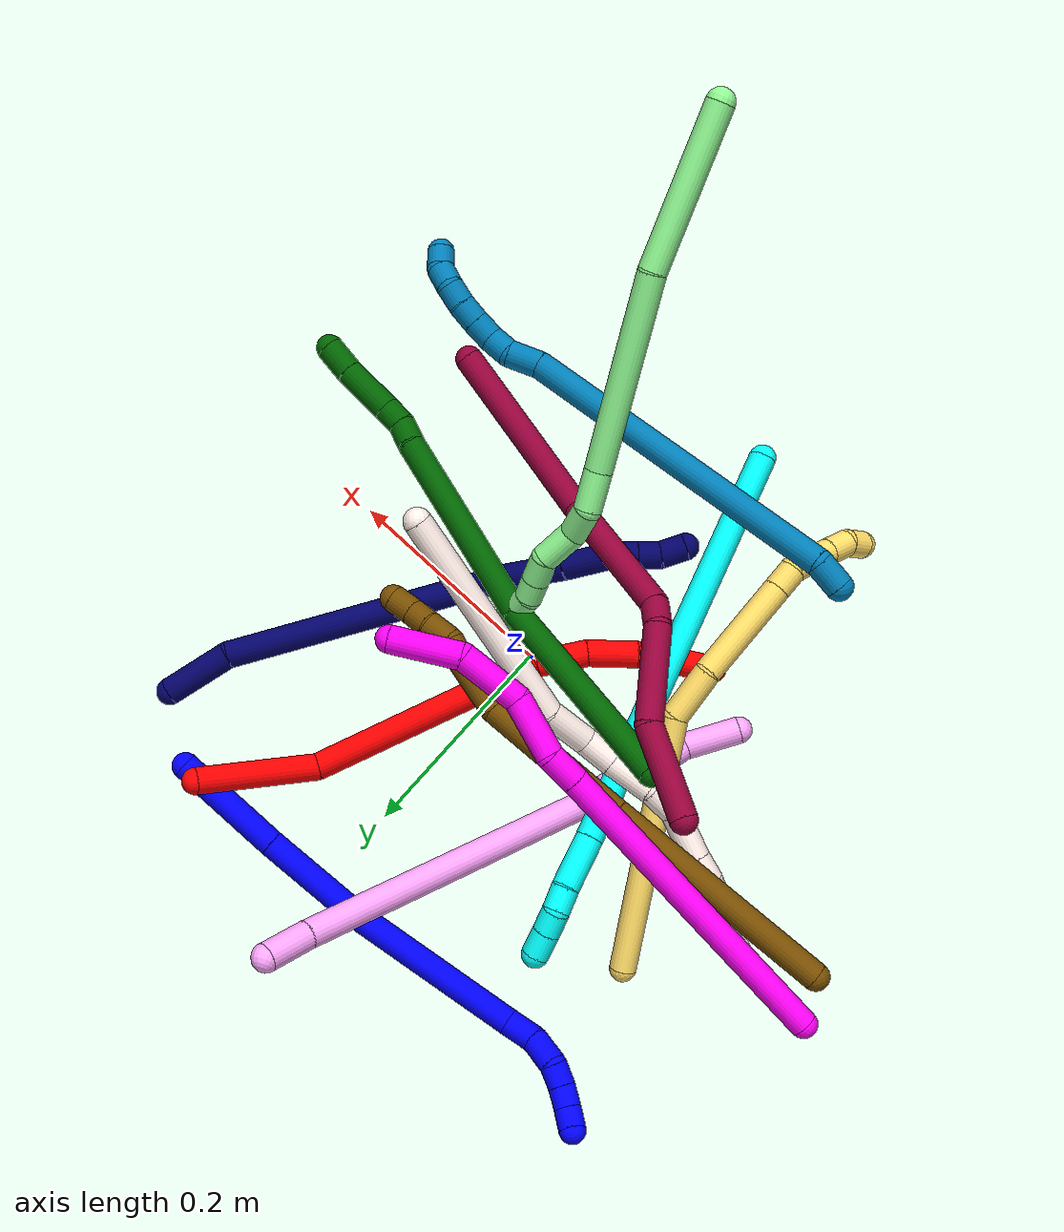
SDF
<sdf version="1.7">
 <world name="default">
  <plugin name="TubeGeneratorPlugin" filename="libtube_generator_plugin.so"/>
  <model name="photoneo_s_sensor">
   <static>1</static>
   <pose>0 0 2 1.57079 1.57079 3.14159</pose>
   <link name="link">
    <inertial><mass>0.1</mass></inertial>
    <sensor name="sensor" type="depth">
     <update_rate>30</update_rate>
     <camera>
      <horizontal_fov>1.22</horizontal_fov>
      <image><width>1920</width><height>1200</height><format>B8G8R8</format></image>
      <clip><near>0.1</near><far>4</far></clip>
      <depth_camera><output>points</output></depth_camera>
     </camera>
     <plugin name="camera_plugin" filename="libgazebo_ros_depth_camera.so">
      <baseline>0.2</baseline>
      <alwaysOn>1</alwaysOn>
      <updateRate>0.0</updateRate>
      <cameraName>camera_ir</cameraName>
      <imageTopicName>/camera/color/image_raw</imageTopicName>
      <cameraInfoTopicName>/camera/color/camera_info</cameraInfoTopicName>
      <depthImageTopicName>/camera/depth/image_raw</depthImageTopicName>
      <depthImageCameraInfoTopicName>/camera/depth/camera_info</depthImageCameraInfoTopicName>
      <pointCloudTopicName>/camera/depth/points</pointCloudTopicName>
      <frameName>fr_optical</frameName>
      <pointCloudCutoff>0.1</pointCloudCutoff>
      <pointCloudCutoffMax>2.0</pointCloudCutoffMax>
      <distortionK1>0</distortionK1>
      <distortionK2>0</distortionK2>
      <distortionK3>0</distortionK3>
      <distortionT1>0</distortionT1>
      <distortionT2>0</distortionT2>
      <CxPrime>0</CxPrime>
      <Cx>0</Cx>
      <Cy>0</Cy>
      <focalLength>0</focalLength>
      <hackBaseline>0</hackBaseline>
     </plugin>
    </sensor>
   </link>
  </model>
  <gravity>0 0 -9.8</gravity>
  <magnetic_field>6e-06 2.3e-05 -4.2e-05</magnetic_field>
  <atmosphere type="adiabatic"/>
  <physics name="default_physics" default="0" type="ode">
   <max_step_size>0.003</max_step_size>
   <real_time_factor>1</real_time_factor>
   <real_time_update_rate>1000</real_time_update_rate>
   <max_contacts>10000</max_contacts>
   <ode>
    <solver>
     <type>quick</type>
     <iters>100</iters>
     <sor>1.3</sor>
     <use_dynamic_moi_rescaling>0</use_dynamic_moi_rescaling>
    </solver>
    <constraints>
     <contact_max_correcting_vel>0</contact_max_correcting_vel>
     <contact_surface_layer>0.001</contact_surface_layer>
     <cfm>0</cfm>
     <erp>0.2</erp>
    </constraints>
   </ode>
  </physics>
  <scene><ambient>0.4 0.4 0.4 1</ambient><background>0.7 0.7 0.7 1</background><shadows>0</shadows></scene>
  <audio><device>default</device></audio>
  <spherical_coordinates>
   <surface_model>EARTH_WGS84</surface_model>
   <latitude_deg>0</latitude_deg>
   <longitude_deg>0</longitude_deg>
   <elevation>0</elevation>
   <heading_deg>0</heading_deg>
  </spherical_coordinates>
  <model name="bin">
   <static>1</static>
   <link name="bottom">
    <collision name="collision-bottom">
     <pose>0 0 -0.01 0 -0 0</pose>
     <geometry><box><size>0.8 0.6 0.02</size></box></geometry>
     <surface>
      <friction><ode><mu>100</mu><mu2>100</mu2></ode></friction>
      <contact><collide_bitmask>65535</collide_bitmask></contact>
     </surface>
    </collision>
   </link>
   <link name="west_wall">
    <collision name="collision-west_wall">
     <pose>-0.41 0 0.1 0 -0 0</pose>
     <geometry><box><size>0.02 0.6 0.2</size></box></geometry>
     <surface>
      <friction><ode><mu>100</mu><mu2>100</mu2></ode></friction>
      <contact><collide_bitmask>65535</collide_bitmask></contact>
     </surface>
    </collision>
   </link>
   <link name="east_wall">
    <collision name="collision-east_wall">
     <pose>0.41 0 0.1 0 -0 0</pose>
     <geometry><box><size>0.02 0.6 0.2</size></box></geometry>
     <surface>
      <friction><ode><mu>100</mu><mu2>100</mu2></ode></friction>
      <contact><collide_bitmask>65535</collide_bitmask></contact>
     </surface>
    </collision>
   </link>
   <link name="south_wall">
    <collision name="collision-south_wall">
     <pose>0 -0.31 0.1 0 -0 0</pose>
     <geometry><box><size>0.8 0.02 0.2</size></box></geometry>
     <surface>
      <friction><ode><mu>100</mu><mu2>100</mu2></ode></friction>
      <contact><collide_bitmask>65535</collide_bitmask></contact>
     </surface>
    </collision>
   </link>
   <link name="north_wall">
    <collision name="collision-north_wall">
     <pose>0 0.31 0.1 0 -0 0</pose>
     <geometry><box><size>0.8 0.02 0.2</size></box></geometry>
     <surface>
      <friction><ode><mu>100</mu><mu2>100</mu2></ode></friction>
      <contact><collide_bitmask>65535</collide_bitmask></contact>
     </surface>
    </collision>
   </link>
  </model>
  <model name="1">
   <static>0</static>
   <link name="1">
    <collision name="collision-cylinder-e_1_1_4">
     <pose>-0.044641 -0.022448 0.01834 0.885773 -0.994871 -0.504125</pose>
     <geometry><cylinder><radius>0.0125</radius><length>0.106454</length></cylinder></geometry>
     <surface>
      <friction><ode><mu>1.16</mu><mu2>1.16</mu2><slip1>0</slip1><slip2>0</slip2></ode></friction>
      <contact><ode><kp>1e+06</kp><kd>1</kd><max_vel>0</max_vel><min_depth>0.001</min_depth></ode></contact>
     </surface>
    </collision>
    <visual name="visual-cylinder-e_1_1_4">
     <pose>-0.044641 -0.022448 0.01834 0.885773 -0.994871 -0.504125</pose>
     <geometry><cylinder><radius>0.0125</radius><length>0.106454</length></cylinder></geometry>
     <material><ambient>0 0 1 1</ambient></material>
    </visual>
    <collision name="collision-cylinder-e_2_4_5">
     <pose>-0.133958 -0.065335 0.055694 0.821518 -1.01234 -0.4738</pose>
     <geometry><cylinder><radius>0.0125</radius><length>0.105361</length></cylinder></geometry>
     <surface>
      <friction><ode><mu>1.16</mu><mu2>1.16</mu2><slip1>0</slip1><slip2>0</slip2></ode></friction>
      <contact><ode><kp>1e+06</kp><kd>1</kd><max_vel>0</max_vel><min_depth>0.001</min_depth></ode></contact>
     </surface>
    </collision>
    <visual name="visual-cylinder-e_2_4_5">
     <pose>-0.133958 -0.065335 0.055694 0.821518 -1.01234 -0.4738</pose>
     <geometry><cylinder><radius>0.0125</radius><length>0.105361</length></cylinder></geometry>
     <material><ambient>0 0 1 1</ambient></material>
    </visual>
    <collision name="collision-cylinder-e_3_5_6">
     <pose>-0.252863 -0.111793 0.102845 0.746294 -1.09418 -0.468172</pose>
     <geometry><cylinder><radius>0.0125</radius><length>0.167076</length></cylinder></geometry>
     <surface>
      <friction><ode><mu>1.16</mu><mu2>1.16</mu2><slip1>0</slip1><slip2>0</slip2></ode></friction>
      <contact><ode><kp>1e+06</kp><kd>1</kd><max_vel>0</max_vel><min_depth>0.001</min_depth></ode></contact>
     </surface>
    </collision>
    <visual name="visual-cylinder-e_3_5_6">
     <pose>-0.252863 -0.111793 0.102845 0.746294 -1.09418 -0.468172</pose>
     <geometry><cylinder><radius>0.0125</radius><length>0.167076</length></cylinder></geometry>
     <material><ambient>0 0 1 1</ambient></material>
    </visual>
    <collision name="collision-cylinder-e_4_6_7">
     <pose>-0.341156 -0.142477 0.130909 1.58685 -1.25056 -1.26584</pose>
     <geometry><cylinder><radius>0.0125</radius><length>0.029636</length></cylinder></geometry>
     <surface>
      <friction><ode><mu>1.16</mu><mu2>1.16</mu2><slip1>0</slip1><slip2>0</slip2></ode></friction>
      <contact><ode><kp>1e+06</kp><kd>1</kd><max_vel>0</max_vel><min_depth>0.001</min_depth></ode></contact>
     </surface>
    </collision>
    <visual name="visual-cylinder-e_4_6_7">
     <pose>-0.341156 -0.142477 0.130909 1.58685 -1.25056 -1.26584</pose>
     <geometry><cylinder><radius>0.0125</radius><length>0.029636</length></cylinder></geometry>
     <material><ambient>0 0 1 1</ambient></material>
    </visual>
    <collision name="collision-cylinder-e_5_7_8">
     <pose>-0.367208 -0.155899 0.128322 1.8502 -0.920935 -1.16445</pose>
     <geometry><cylinder><radius>0.0125</radius><length>0.030114</length></cylinder></geometry>
     <surface>
      <friction><ode><mu>1.16</mu><mu2>1.16</mu2><slip1>0</slip1><slip2>0</slip2></ode></friction>
      <contact><ode><kp>1e+06</kp><kd>1</kd><max_vel>0</max_vel><min_depth>0.001</min_depth></ode></contact>
     </surface>
    </collision>
    <visual name="visual-cylinder-e_5_7_8">
     <pose>-0.367208 -0.155899 0.128322 1.8502 -0.920935 -1.16445</pose>
     <geometry><cylinder><radius>0.0125</radius><length>0.030114</length></cylinder></geometry>
     <material><ambient>0 0 1 1</ambient></material>
    </visual>
    <collision name="collision-cylinder-e_6_8_9">
     <pose>-0.385265 -0.172947 0.127696 1.34702 -0.619885 -0.500421</pose>
     <geometry><cylinder><radius>0.0125</radius><length>0.020893</length></cylinder></geometry>
     <surface>
      <friction><ode><mu>1.16</mu><mu2>1.16</mu2><slip1>0</slip1><slip2>0</slip2></ode></friction>
      <contact><ode><kp>1e+06</kp><kd>1</kd><max_vel>0</max_vel><min_depth>0.001</min_depth></ode></contact>
     </surface>
    </collision>
    <visual name="visual-cylinder-e_6_8_9">
     <pose>-0.385265 -0.172947 0.127696 1.34702 -0.619885 -0.500421</pose>
     <geometry><cylinder><radius>0.0125</radius><length>0.020893</length></cylinder></geometry>
     <material><ambient>0 0 1 1</ambient></material>
    </visual>
    <collision name="collision-cylinder-e_7_9_10">
     <pose>-0.396492 -0.190038 0.130012 1.52209 -0.529621 -0.505515</pose>
     <geometry><cylinder><radius>0.0125</radius><length>0.02042</length></cylinder></geometry>
     <surface>
      <friction><ode><mu>1.16</mu><mu2>1.16</mu2><slip1>0</slip1><slip2>0</slip2></ode></friction>
      <contact><ode><kp>1e+06</kp><kd>1</kd><max_vel>0</max_vel><min_depth>0.001</min_depth></ode></contact>
     </surface>
    </collision>
    <visual name="visual-cylinder-e_7_9_10">
     <pose>-0.396492 -0.190038 0.130012 1.52209 -0.529621 -0.505515</pose>
     <geometry><cylinder><radius>0.0125</radius><length>0.02042</length></cylinder></geometry>
     <material><ambient>0 0 1 1</ambient></material>
    </visual>
    <collision name="collision-cylinder-e_8_10_2">
     <pose>-0.406578 -0.207405 0.12877 1.76343 -0.514064 -0.617717</pose>
     <geometry><cylinder><radius>0.0125</radius><length>0.020047</length></cylinder></geometry>
     <surface>
      <friction><ode><mu>1.16</mu><mu2>1.16</mu2><slip1>0</slip1><slip2>0</slip2></ode></friction>
      <contact><ode><kp>1e+06</kp><kd>1</kd><max_vel>0</max_vel><min_depth>0.001</min_depth></ode></contact>
     </surface>
    </collision>
    <visual name="visual-cylinder-e_8_10_2">
     <pose>-0.406578 -0.207405 0.12877 1.76343 -0.514064 -0.617717</pose>
     <geometry><cylinder><radius>0.0125</radius><length>0.020047</length></cylinder></geometry>
     <material><ambient>0 0 1 1</ambient></material>
    </visual>
    <collision name="collision-sphere-2">
     <pose>-0.411507 -0.215972 0.127099 0 -0 0</pose>
     <geometry><sphere><radius>0.0125</radius></sphere></geometry>
     <surface>
      <friction><ode><mu>1.16</mu><mu2>1.16</mu2><slip1>0</slip1><slip2>0</slip2></ode></friction>
      <contact><ode><kp>1e+06</kp><kd>1</kd><max_vel>0</max_vel><min_depth>0.001</min_depth></ode></contact>
     </surface>
    </collision>
    <visual name="visual-sphere-2">
     <pose>-0.411507 -0.215972 0.127099 0 -0 0</pose>
     <geometry><sphere><radius>0.0125</radius></sphere></geometry>
     <material><ambient>0 0 1 1</ambient></material>
    </visual>
    <collision name="collision-sphere-10">
     <pose>-0.40165 -0.198839 0.130441 0 -0 0</pose>
     <geometry><sphere><radius>0.0125</radius></sphere></geometry>
     <surface>
      <friction><ode><mu>1.16</mu><mu2>1.16</mu2><slip1>0</slip1><slip2>0</slip2></ode></friction>
      <contact><ode><kp>1e+06</kp><kd>1</kd><max_vel>0</max_vel><min_depth>0.001</min_depth></ode></contact>
     </surface>
    </collision>
    <visual name="visual-sphere-10">
     <pose>-0.40165 -0.198839 0.130441 0 -0 0</pose>
     <geometry><sphere><radius>0.0125</radius></sphere></geometry>
     <material><ambient>0 0 1 1</ambient></material>
    </visual>
    <collision name="collision-sphere-9">
     <pose>-0.391334 -0.181238 0.129583 0 -0 0</pose>
     <geometry><sphere><radius>0.0125</radius></sphere></geometry>
     <surface>
      <friction><ode><mu>1.16</mu><mu2>1.16</mu2><slip1>0</slip1><slip2>0</slip2></ode></friction>
      <contact><ode><kp>1e+06</kp><kd>1</kd><max_vel>0</max_vel><min_depth>0.001</min_depth></ode></contact>
     </surface>
    </collision>
    <visual name="visual-sphere-9">
     <pose>-0.391334 -0.181238 0.129583 0 -0 0</pose>
     <geometry><sphere><radius>0.0125</radius></sphere></geometry>
     <material><ambient>0 0 1 1</ambient></material>
    </visual>
    <collision name="collision-sphere-4">
     <pose>-0.089282 -0.044897 0.036681 0 -0 0</pose>
     <geometry><sphere><radius>0.0125</radius></sphere></geometry>
     <surface>
      <friction><ode><mu>1.16</mu><mu2>1.16</mu2><slip1>0</slip1><slip2>0</slip2></ode></friction>
      <contact><ode><kp>1e+06</kp><kd>1</kd><max_vel>0</max_vel><min_depth>0.001</min_depth></ode></contact>
     </surface>
    </collision>
    <visual name="visual-sphere-4">
     <pose>-0.089282 -0.044897 0.036681 0 -0 0</pose>
     <geometry><sphere><radius>0.0125</radius></sphere></geometry>
     <material><ambient>0 0 1 1</ambient></material>
    </visual>
    <collision name="collision-sphere-1">
     <geometry><sphere><radius>0.0125</radius></sphere></geometry>
     <surface>
      <friction><ode><mu>1.16</mu><mu2>1.16</mu2><slip1>0</slip1><slip2>0</slip2></ode></friction>
      <contact><ode><kp>1e+06</kp><kd>1</kd><max_vel>0</max_vel><min_depth>0.001</min_depth></ode></contact>
     </surface>
    </collision>
    <visual name="visual-sphere-1">
     <geometry><sphere><radius>0.0125</radius></sphere></geometry>
     <material><ambient>0 0 1 1</ambient></material>
    </visual>
    <collision name="collision-sphere-8">
     <pose>-0.379196 -0.164656 0.125809 0 -0 0</pose>
     <geometry><sphere><radius>0.0125</radius></sphere></geometry>
     <surface>
      <friction><ode><mu>1.16</mu><mu2>1.16</mu2><slip1>0</slip1><slip2>0</slip2></ode></friction>
      <contact><ode><kp>1e+06</kp><kd>1</kd><max_vel>0</max_vel><min_depth>0.001</min_depth></ode></contact>
     </surface>
    </collision>
    <visual name="visual-sphere-8">
     <pose>-0.379196 -0.164656 0.125809 0 -0 0</pose>
     <geometry><sphere><radius>0.0125</radius></sphere></geometry>
     <material><ambient>0 0 1 1</ambient></material>
    </visual>
    <collision name="collision-sphere-5">
     <pose>-0.178635 -0.085773 0.074706 0 -0 0</pose>
     <geometry><sphere><radius>0.0125</radius></sphere></geometry>
     <surface>
      <friction><ode><mu>1.16</mu><mu2>1.16</mu2><slip1>0</slip1><slip2>0</slip2></ode></friction>
      <contact><ode><kp>1e+06</kp><kd>1</kd><max_vel>0</max_vel><min_depth>0.001</min_depth></ode></contact>
     </surface>
    </collision>
    <visual name="visual-sphere-5">
     <pose>-0.178635 -0.085773 0.074706 0 -0 0</pose>
     <geometry><sphere><radius>0.0125</radius></sphere></geometry>
     <material><ambient>0 0 1 1</ambient></material>
    </visual>
    <collision name="collision-sphere-6">
     <pose>-0.327091 -0.137813 0.130984 0 -0 0</pose>
     <geometry><sphere><radius>0.0125</radius></sphere></geometry>
     <surface>
      <friction><ode><mu>1.16</mu><mu2>1.16</mu2><slip1>0</slip1><slip2>0</slip2></ode></friction>
      <contact><ode><kp>1e+06</kp><kd>1</kd><max_vel>0</max_vel><min_depth>0.001</min_depth></ode></contact>
     </surface>
    </collision>
    <visual name="visual-sphere-6">
     <pose>-0.327091 -0.137813 0.130984 0 -0 0</pose>
     <geometry><sphere><radius>0.0125</radius></sphere></geometry>
     <material><ambient>0 0 1 1</ambient></material>
    </visual>
    <collision name="collision-sphere-7">
     <pose>-0.35522 -0.147141 0.130834 0 -0 0</pose>
     <geometry><sphere><radius>0.0125</radius></sphere></geometry>
     <surface>
      <friction><ode><mu>1.16</mu><mu2>1.16</mu2><slip1>0</slip1><slip2>0</slip2></ode></friction>
      <contact><ode><kp>1e+06</kp><kd>1</kd><max_vel>0</max_vel><min_depth>0.001</min_depth></ode></contact>
     </surface>
    </collision>
    <visual name="visual-sphere-7">
     <pose>-0.35522 -0.147141 0.130834 0 -0 0</pose>
     <geometry><sphere><radius>0.0125</radius></sphere></geometry>
     <material><ambient>0 0 1 1</ambient></material>
    </visual>
    <inertial>
     <pose>-0.213156 -0.097041 0.081303 0 -0 0</pose>
     <mass>0.5</mass>
     <inertia>
      <ixx>9.3e-05</ixx>
      <ixy>0</ixy>
      <ixz>0</ixz>
      <iyy>0.000398</iyy>
      <iyz>0</iyz>
      <izz>0.000757</izz>
     </inertia>
    </inertial>
   </link>
   <pose>0.167372 0.287567 0.011493 -2.86855 0.266804 0.527613</pose>
  </model>
  <model name="2">
   <static>0</static>
   <link name="2">
    <collision name="collision-cylinder-e_1_1_4">
     <pose>-0.013054 -0.012299 -0.053739 2.91661 -0.232515 -1.60399</pose>
     <geometry><cylinder><radius>0.0125</radius><length>0.113305</length></cylinder></geometry>
     <surface>
      <friction><ode><mu>1.16</mu><mu2>1.16</mu2><slip1>0</slip1><slip2>0</slip2></ode></friction>
      <contact><ode><kp>1e+06</kp><kd>1</kd><max_vel>0</max_vel><min_depth>0.001</min_depth></ode></contact>
     </surface>
    </collision>
    <visual name="visual-cylinder-e_1_1_4">
     <pose>-0.013054 -0.012299 -0.053739 2.91661 -0.232515 -1.60399</pose>
     <geometry><cylinder><radius>0.0125</radius><length>0.113305</length></cylinder></geometry>
     <material><ambient>1 0 0 1</ambient></material>
    </visual>
    <collision name="collision-cylinder-e_2_4_5">
     <pose>-0.048247 -0.097992 -0.187482 2.39925 -0.201154 -0.507403</pose>
     <geometry><cylinder><radius>0.0125</radius><length>0.221609</length></cylinder></geometry>
     <surface>
      <friction><ode><mu>1.16</mu><mu2>1.16</mu2><slip1>0</slip1><slip2>0</slip2></ode></friction>
      <contact><ode><kp>1e+06</kp><kd>1</kd><max_vel>0</max_vel><min_depth>0.001</min_depth></ode></contact>
     </surface>
    </collision>
    <visual name="visual-cylinder-e_2_4_5">
     <pose>-0.048247 -0.097992 -0.187482 2.39925 -0.201154 -0.507403</pose>
     <geometry><cylinder><radius>0.0125</radius><length>0.221609</length></cylinder></geometry>
     <material><ambient>1 0 0 1</ambient></material>
    </visual>
    <collision name="collision-cylinder-e_3_5_6">
     <pose>-0.078075 -0.182438 -0.287732 2.64197 -0.321769 -1.13303</pose>
     <geometry><cylinder><radius>0.0125</radius><length>0.048627</length></cylinder></geometry>
     <surface>
      <friction><ode><mu>1.16</mu><mu2>1.16</mu2><slip1>0</slip1><slip2>0</slip2></ode></friction>
      <contact><ode><kp>1e+06</kp><kd>1</kd><max_vel>0</max_vel><min_depth>0.001</min_depth></ode></contact>
     </surface>
    </collision>
    <visual name="visual-cylinder-e_3_5_6">
     <pose>-0.078075 -0.182438 -0.287732 2.64197 -0.321769 -1.13303</pose>
     <geometry><cylinder><radius>0.0125</radius><length>0.048627</length></cylinder></geometry>
     <material><ambient>1 0 0 1</ambient></material>
    </visual>
    <collision name="collision-cylinder-e_4_6_7">
     <pose>-0.098835 -0.202162 -0.325275 2.67677 -0.594118 -1.82523</pose>
     <geometry><cylinder><radius>0.0125</radius><length>0.046702</length></cylinder></geometry>
     <surface>
      <friction><ode><mu>1.16</mu><mu2>1.16</mu2><slip1>0</slip1><slip2>0</slip2></ode></friction>
      <contact><ode><kp>1e+06</kp><kd>1</kd><max_vel>0</max_vel><min_depth>0.001</min_depth></ode></contact>
     </surface>
    </collision>
    <visual name="visual-cylinder-e_4_6_7">
     <pose>-0.098835 -0.202162 -0.325275 2.67677 -0.594118 -1.82523</pose>
     <geometry><cylinder><radius>0.0125</radius><length>0.046702</length></cylinder></geometry>
     <material><ambient>1 0 0 1</ambient></material>
    </visual>
    <collision name="collision-cylinder-e_5_7_8">
     <pose>-0.117844 -0.213479 -0.350289 2.81158 -0.629156 -2.19555</pose>
     <geometry><cylinder><radius>0.0125</radius><length>0.020178</length></cylinder></geometry>
     <surface>
      <friction><ode><mu>1.16</mu><mu2>1.16</mu2><slip1>0</slip1><slip2>0</slip2></ode></friction>
      <contact><ode><kp>1e+06</kp><kd>1</kd><max_vel>0</max_vel><min_depth>0.001</min_depth></ode></contact>
     </surface>
    </collision>
    <visual name="visual-cylinder-e_5_7_8">
     <pose>-0.117844 -0.213479 -0.350289 2.81158 -0.629156 -2.19555</pose>
     <geometry><cylinder><radius>0.0125</radius><length>0.020178</length></cylinder></geometry>
     <material><ambient>1 0 0 1</ambient></material>
    </visual>
    <collision name="collision-cylinder-e_6_8_2">
     <pose>-0.139559 -0.220409 -0.376639 2.91553 -0.689923 -2.52961</pose>
     <geometry><cylinder><radius>0.0125</radius><length>0.049579</length></cylinder></geometry>
     <surface>
      <friction><ode><mu>1.16</mu><mu2>1.16</mu2><slip1>0</slip1><slip2>0</slip2></ode></friction>
      <contact><ode><kp>1e+06</kp><kd>1</kd><max_vel>0</max_vel><min_depth>0.001</min_depth></ode></contact>
     </surface>
    </collision>
    <visual name="visual-cylinder-e_6_8_2">
     <pose>-0.139559 -0.220409 -0.376639 2.91553 -0.689923 -2.52961</pose>
     <geometry><cylinder><radius>0.0125</radius><length>0.049579</length></cylinder></geometry>
     <material><ambient>1 0 0 1</ambient></material>
    </visual>
    <collision name="collision-sphere-2">
     <pose>-0.155337 -0.224694 -0.395273 0 -0 0</pose>
     <geometry><sphere><radius>0.0125</radius></sphere></geometry>
     <surface>
      <friction><ode><mu>1.16</mu><mu2>1.16</mu2><slip1>0</slip1><slip2>0</slip2></ode></friction>
      <contact><ode><kp>1e+06</kp><kd>1</kd><max_vel>0</max_vel><min_depth>0.001</min_depth></ode></contact>
     </surface>
    </collision>
    <visual name="visual-sphere-2">
     <pose>-0.155337 -0.224694 -0.395273 0 -0 0</pose>
     <geometry><sphere><radius>0.0125</radius></sphere></geometry>
     <material><ambient>1 0 0 1</ambient></material>
    </visual>
    <collision name="collision-sphere-4">
     <pose>-0.026108 -0.024598 -0.107477 0 -0 0</pose>
     <geometry><sphere><radius>0.0125</radius></sphere></geometry>
     <surface>
      <friction><ode><mu>1.16</mu><mu2>1.16</mu2><slip1>0</slip1><slip2>0</slip2></ode></friction>
      <contact><ode><kp>1e+06</kp><kd>1</kd><max_vel>0</max_vel><min_depth>0.001</min_depth></ode></contact>
     </surface>
    </collision>
    <visual name="visual-sphere-4">
     <pose>-0.026108 -0.024598 -0.107477 0 -0 0</pose>
     <geometry><sphere><radius>0.0125</radius></sphere></geometry>
     <material><ambient>1 0 0 1</ambient></material>
    </visual>
    <collision name="collision-sphere-1">
     <geometry><sphere><radius>0.0125</radius></sphere></geometry>
     <surface>
      <friction><ode><mu>1.16</mu><mu2>1.16</mu2><slip1>0</slip1><slip2>0</slip2></ode></friction>
      <contact><ode><kp>1e+06</kp><kd>1</kd><max_vel>0</max_vel><min_depth>0.001</min_depth></ode></contact>
     </surface>
    </collision>
    <visual name="visual-sphere-1">
     <geometry><sphere><radius>0.0125</radius></sphere></geometry>
     <material><ambient>1 0 0 1</ambient></material>
    </visual>
    <collision name="collision-sphere-8">
     <pose>-0.123781 -0.216123 -0.358006 0 -0 0</pose>
     <geometry><sphere><radius>0.0125</radius></sphere></geometry>
     <surface>
      <friction><ode><mu>1.16</mu><mu2>1.16</mu2><slip1>0</slip1><slip2>0</slip2></ode></friction>
      <contact><ode><kp>1e+06</kp><kd>1</kd><max_vel>0</max_vel><min_depth>0.001</min_depth></ode></contact>
     </surface>
    </collision>
    <visual name="visual-sphere-8">
     <pose>-0.123781 -0.216123 -0.358006 0 -0 0</pose>
     <geometry><sphere><radius>0.0125</radius></sphere></geometry>
     <material><ambient>1 0 0 1</ambient></material>
    </visual>
    <collision name="collision-sphere-5">
     <pose>-0.070386 -0.171387 -0.267486 0 -0 0</pose>
     <geometry><sphere><radius>0.0125</radius></sphere></geometry>
     <surface>
      <friction><ode><mu>1.16</mu><mu2>1.16</mu2><slip1>0</slip1><slip2>0</slip2></ode></friction>
      <contact><ode><kp>1e+06</kp><kd>1</kd><max_vel>0</max_vel><min_depth>0.001</min_depth></ode></contact>
     </surface>
    </collision>
    <visual name="visual-sphere-5">
     <pose>-0.070386 -0.171387 -0.267486 0 -0 0</pose>
     <geometry><sphere><radius>0.0125</radius></sphere></geometry>
     <material><ambient>1 0 0 1</ambient></material>
    </visual>
    <collision name="collision-sphere-6">
     <pose>-0.085764 -0.193488 -0.307978 0 -0 0</pose>
     <geometry><sphere><radius>0.0125</radius></sphere></geometry>
     <surface>
      <friction><ode><mu>1.16</mu><mu2>1.16</mu2><slip1>0</slip1><slip2>0</slip2></ode></friction>
      <contact><ode><kp>1e+06</kp><kd>1</kd><max_vel>0</max_vel><min_depth>0.001</min_depth></ode></contact>
     </surface>
    </collision>
    <visual name="visual-sphere-6">
     <pose>-0.085764 -0.193488 -0.307978 0 -0 0</pose>
     <geometry><sphere><radius>0.0125</radius></sphere></geometry>
     <material><ambient>1 0 0 1</ambient></material>
    </visual>
    <collision name="collision-sphere-7">
     <pose>-0.111907 -0.210836 -0.342571 0 -0 0</pose>
     <geometry><sphere><radius>0.0125</radius></sphere></geometry>
     <surface>
      <friction><ode><mu>1.16</mu><mu2>1.16</mu2><slip1>0</slip1><slip2>0</slip2></ode></friction>
      <contact><ode><kp>1e+06</kp><kd>1</kd><max_vel>0</max_vel><min_depth>0.001</min_depth></ode></contact>
     </surface>
    </collision>
    <visual name="visual-sphere-7">
     <pose>-0.111907 -0.210836 -0.342571 0 -0 0</pose>
     <geometry><sphere><radius>0.0125</radius></sphere></geometry>
     <material><ambient>1 0 0 1</ambient></material>
    </visual>
    <inertial>
     <pose>-0.059761 -0.113315 -0.205121 0 -0 0</pose>
     <mass>0.5</mass>
     <inertia>
      <ixx>0.000179</ixx>
      <ixy>0</ixy>
      <ixz>0</ixz>
      <iyy>-0.001105</iyy>
      <iyz>0</iyz>
      <izz>0.000844</izz>
     </inertia>
    </inertial>
   </link>
   <pose>0.148041 0.285258 0.050885 -0.720424 0.582074 -0.165413</pose>
  </model>
  <model name="3">
   <static>0</static>
   <link name="3">
    <collision name="collision-cylinder-e_1_1_4">
     <pose>-0.020773 0.160827 0.103542 -0.998784 -0.10818 0.059054</pose>
     <geometry><cylinder><radius>0.0125</radius><length>0.3848</length></cylinder></geometry>
     <surface>
      <friction><ode><mu>1.16</mu><mu2>1.16</mu2><slip1>0</slip1><slip2>0</slip2></ode></friction>
      <contact><ode><kp>1e+06</kp><kd>1</kd><max_vel>0</max_vel><min_depth>0.001</min_depth></ode></contact>
     </surface>
    </collision>
    <visual name="visual-cylinder-e_1_1_4">
     <pose>-0.020773 0.160827 0.103542 -0.998784 -0.10818 0.059054</pose>
     <geometry><cylinder><radius>0.0125</radius><length>0.3848</length></cylinder></geometry>
     <material><ambient>0.003922 1 0.996078 1</ambient></material>
    </visual>
    <collision name="collision-cylinder-e_2_4_5">
     <pose>-0.043841 0.34127 0.221126 -0.949511 -0.094819 0.04876</pose>
     <geometry><cylinder><radius>0.0125</radius><length>0.048466</length></cylinder></geometry>
     <surface>
      <friction><ode><mu>1.16</mu><mu2>1.16</mu2><slip1>0</slip1><slip2>0</slip2></ode></friction>
      <contact><ode><kp>1e+06</kp><kd>1</kd><max_vel>0</max_vel><min_depth>0.001</min_depth></ode></contact>
     </surface>
    </collision>
    <visual name="visual-cylinder-e_2_4_5">
     <pose>-0.043841 0.34127 0.221126 -0.949511 -0.094819 0.04876</pose>
     <geometry><cylinder><radius>0.0125</radius><length>0.048466</length></cylinder></geometry>
     <material><ambient>0.003922 1 0.996078 1</ambient></material>
    </visual>
    <collision name="collision-cylinder-e_3_5_6">
     <pose>-0.047539 0.370578 0.240147 -1.09628 -0.128161 0.078316</pose>
     <geometry><cylinder><radius>0.0125</radius><length>0.021972</length></cylinder></geometry>
     <surface>
      <friction><ode><mu>1.16</mu><mu2>1.16</mu2><slip1>0</slip1><slip2>0</slip2></ode></friction>
      <contact><ode><kp>1e+06</kp><kd>1</kd><max_vel>0</max_vel><min_depth>0.001</min_depth></ode></contact>
     </surface>
    </collision>
    <visual name="visual-cylinder-e_3_5_6">
     <pose>-0.047539 0.370578 0.240147 -1.09628 -0.128161 0.078316</pose>
     <geometry><cylinder><radius>0.0125</radius><length>0.021972</length></cylinder></geometry>
     <material><ambient>0.003922 1 0.996078 1</ambient></material>
    </visual>
    <collision name="collision-cylinder-e_4_6_7">
     <pose>-0.048697 0.39068 0.246556 -1.43425 0.023457 -0.020454</pose>
     <geometry><cylinder><radius>0.0125</radius><length>0.021021</length></cylinder></geometry>
     <surface>
      <friction><ode><mu>1.16</mu><mu2>1.16</mu2><slip1>0</slip1><slip2>0</slip2></ode></friction>
      <contact><ode><kp>1e+06</kp><kd>1</kd><max_vel>0</max_vel><min_depth>0.001</min_depth></ode></contact>
     </surface>
    </collision>
    <visual name="visual-cylinder-e_4_6_7">
     <pose>-0.048697 0.39068 0.246556 -1.43425 0.023457 -0.020454</pose>
     <geometry><cylinder><radius>0.0125</radius><length>0.021021</length></cylinder></geometry>
     <material><ambient>0.003922 1 0.996078 1</ambient></material>
    </visual>
    <collision name="collision-cylinder-e_5_7_2">
     <pose>-0.047912 0.412819 0.249725 -1.42361 0.045369 -0.03914</pose>
     <geometry><cylinder><radius>0.0125</radius><length>0.023741</length></cylinder></geometry>
     <surface>
      <friction><ode><mu>1.16</mu><mu2>1.16</mu2><slip1>0</slip1><slip2>0</slip2></ode></friction>
      <contact><ode><kp>1e+06</kp><kd>1</kd><max_vel>0</max_vel><min_depth>0.001</min_depth></ode></contact>
     </surface>
    </collision>
    <visual name="visual-cylinder-e_5_7_2">
     <pose>-0.047912 0.412819 0.249725 -1.42361 0.045369 -0.03914</pose>
     <geometry><cylinder><radius>0.0125</radius><length>0.023741</length></cylinder></geometry>
     <material><ambient>0.003922 1 0.996078 1</ambient></material>
    </visual>
    <collision name="collision-sphere-2">
     <pose>-0.047374 0.42455 0.251464 0 -0 0</pose>
     <geometry><sphere><radius>0.0125</radius></sphere></geometry>
     <surface>
      <friction><ode><mu>1.16</mu><mu2>1.16</mu2><slip1>0</slip1><slip2>0</slip2></ode></friction>
      <contact><ode><kp>1e+06</kp><kd>1</kd><max_vel>0</max_vel><min_depth>0.001</min_depth></ode></contact>
     </surface>
    </collision>
    <visual name="visual-sphere-2">
     <pose>-0.047374 0.42455 0.251464 0 -0 0</pose>
     <geometry><sphere><radius>0.0125</radius></sphere></geometry>
     <material><ambient>0.003922 1 0.996078 1</ambient></material>
    </visual>
    <collision name="collision-sphere-7">
     <pose>-0.04845 0.401089 0.247986 0 -0 0</pose>
     <geometry><sphere><radius>0.0125</radius></sphere></geometry>
     <surface>
      <friction><ode><mu>1.16</mu><mu2>1.16</mu2><slip1>0</slip1><slip2>0</slip2></ode></friction>
      <contact><ode><kp>1e+06</kp><kd>1</kd><max_vel>0</max_vel><min_depth>0.001</min_depth></ode></contact>
     </surface>
    </collision>
    <visual name="visual-sphere-7">
     <pose>-0.04845 0.401089 0.247986 0 -0 0</pose>
     <geometry><sphere><radius>0.0125</radius></sphere></geometry>
     <material><ambient>0.003922 1 0.996078 1</ambient></material>
    </visual>
    <collision name="collision-sphere-6">
     <pose>-0.048943 0.38027 0.245125 0 -0 0</pose>
     <geometry><sphere><radius>0.0125</radius></sphere></geometry>
     <surface>
      <friction><ode><mu>1.16</mu><mu2>1.16</mu2><slip1>0</slip1><slip2>0</slip2></ode></friction>
      <contact><ode><kp>1e+06</kp><kd>1</kd><max_vel>0</max_vel><min_depth>0.001</min_depth></ode></contact>
     </surface>
    </collision>
    <visual name="visual-sphere-6">
     <pose>-0.048943 0.38027 0.245125 0 -0 0</pose>
     <geometry><sphere><radius>0.0125</radius></sphere></geometry>
     <material><ambient>0.003922 1 0.996078 1</ambient></material>
    </visual>
    <collision name="collision-sphere-5">
     <pose>-0.046135 0.360886 0.235168 0 -0 0</pose>
     <geometry><sphere><radius>0.0125</radius></sphere></geometry>
     <surface>
      <friction><ode><mu>1.16</mu><mu2>1.16</mu2><slip1>0</slip1><slip2>0</slip2></ode></friction>
      <contact><ode><kp>1e+06</kp><kd>1</kd><max_vel>0</max_vel><min_depth>0.001</min_depth></ode></contact>
     </surface>
    </collision>
    <visual name="visual-sphere-5">
     <pose>-0.046135 0.360886 0.235168 0 -0 0</pose>
     <geometry><sphere><radius>0.0125</radius></sphere></geometry>
     <material><ambient>0.003922 1 0.996078 1</ambient></material>
    </visual>
    <collision name="collision-sphere-1">
     <geometry><sphere><radius>0.0125</radius></sphere></geometry>
     <surface>
      <friction><ode><mu>1.16</mu><mu2>1.16</mu2><slip1>0</slip1><slip2>0</slip2></ode></friction>
      <contact><ode><kp>1e+06</kp><kd>1</kd><max_vel>0</max_vel><min_depth>0.001</min_depth></ode></contact>
     </surface>
    </collision>
    <visual name="visual-sphere-1">
     <geometry><sphere><radius>0.0125</radius></sphere></geometry>
     <material><ambient>0.003922 1 0.996078 1</ambient></material>
    </visual>
    <collision name="collision-sphere-4">
     <pose>-0.041546 0.321654 0.207084 0 -0 0</pose>
     <geometry><sphere><radius>0.0125</radius></sphere></geometry>
     <surface>
      <friction><ode><mu>1.16</mu><mu2>1.16</mu2><slip1>0</slip1><slip2>0</slip2></ode></friction>
      <contact><ode><kp>1e+06</kp><kd>1</kd><max_vel>0</max_vel><min_depth>0.001</min_depth></ode></contact>
     </surface>
    </collision>
    <visual name="visual-sphere-4">
     <pose>-0.041546 0.321654 0.207084 0 -0 0</pose>
     <geometry><sphere><radius>0.0125</radius></sphere></geometry>
     <material><ambient>0.003922 1 0.996078 1</ambient></material>
    </visual>
    <inertial>
     <pose>-0.026648 0.209163 0.133896 0 -0 0</pose>
     <mass>0.5</mass>
     <inertia>
      <ixx>0.00502</ixx>
      <ixy>0</ixy>
      <ixz>0</ixz>
      <iyy>0.002921</iyy>
      <iyz>0</iyz>
      <izz>-0.003461</izz>
     </inertia>
    </inertial>
   </link>
   <pose>-0.034795 -0.277907 0.01247 -0.406849 0.355201 0.250322</pose>
  </model>
  <model name="4">
   <static>0</static>
   <link name="4">
    <collision name="collision-cylinder-e_1_1_4">
     <pose>-0.008717 -0.010937 -0.015253 2.51955 -0.434778 -1.20406</pose>
     <geometry><cylinder><radius>0.0125</radius><length>0.041388</length></cylinder></geometry>
     <surface>
      <friction><ode><mu>1.16</mu><mu2>1.16</mu2><slip1>0</slip1><slip2>0</slip2></ode></friction>
      <contact><ode><kp>1e+06</kp><kd>1</kd><max_vel>0</max_vel><min_depth>0.001</min_depth></ode></contact>
     </surface>
    </collision>
    <visual name="visual-cylinder-e_1_1_4">
     <pose>-0.008717 -0.010937 -0.015253 2.51955 -0.434778 -1.20406</pose>
     <geometry><cylinder><radius>0.0125</radius><length>0.041388</length></cylinder></geometry>
     <material><ambient>1 0.65098 0.996078 1</ambient></material>
    </visual>
    <collision name="collision-cylinder-e_2_4_5">
     <pose>-0.070696 -0.108223 -0.131743 2.43539 -0.380756 -0.963587</pose>
     <geometry><cylinder><radius>0.0125</radius><length>0.28665</length></cylinder></geometry>
     <surface>
      <friction><ode><mu>1.16</mu><mu2>1.16</mu2><slip1>0</slip1><slip2>0</slip2></ode></friction>
      <contact><ode><kp>1e+06</kp><kd>1</kd><max_vel>0</max_vel><min_depth>0.001</min_depth></ode></contact>
     </surface>
    </collision>
    <visual name="visual-cylinder-e_2_4_5">
     <pose>-0.070696 -0.108223 -0.131743 2.43539 -0.380756 -0.963587</pose>
     <geometry><cylinder><radius>0.0125</radius><length>0.28665</length></cylinder></geometry>
     <material><ambient>1 0.65098 0.996078 1</ambient></material>
    </visual>
    <collision name="collision-cylinder-e_3_5_6">
     <pose>-0.129268 -0.207157 -0.252441 2.56761 -0.225188 -0.73173</pose>
     <geometry><cylinder><radius>0.0125</radius><length>0.047552</length></cylinder></geometry>
     <surface>
      <friction><ode><mu>1.16</mu><mu2>1.16</mu2><slip1>0</slip1><slip2>0</slip2></ode></friction>
      <contact><ode><kp>1e+06</kp><kd>1</kd><max_vel>0</max_vel><min_depth>0.001</min_depth></ode></contact>
     </surface>
    </collision>
    <visual name="visual-cylinder-e_3_5_6">
     <pose>-0.129268 -0.207157 -0.252441 2.56761 -0.225188 -0.73173</pose>
     <geometry><cylinder><radius>0.0125</radius><length>0.047552</length></cylinder></geometry>
     <material><ambient>1 0.65098 0.996078 1</ambient></material>
    </visual>
    <collision name="collision-cylinder-e_4_6_7">
     <pose>-0.142203 -0.233685 -0.285127 2.32972 -0.377798 -0.83704</pose>
     <geometry><cylinder><radius>0.0125</radius><length>0.041352</length></cylinder></geometry>
     <surface>
      <friction><ode><mu>1.16</mu><mu2>1.16</mu2><slip1>0</slip1><slip2>0</slip2></ode></friction>
      <contact><ode><kp>1e+06</kp><kd>1</kd><max_vel>0</max_vel><min_depth>0.001</min_depth></ode></contact>
     </surface>
    </collision>
    <visual name="visual-cylinder-e_4_6_7">
     <pose>-0.142203 -0.233685 -0.285127 2.32972 -0.377798 -0.83704</pose>
     <geometry><cylinder><radius>0.0125</radius><length>0.041352</length></cylinder></geometry>
     <material><ambient>1 0.65098 0.996078 1</ambient></material>
    </visual>
    <collision name="collision-cylinder-e_5_7_8">
     <pose>-0.153117 -0.255922 -0.310348 2.5368 -0.221691 -0.6854</pose>
     <geometry><cylinder><radius>0.0125</radius><length>0.029899</length></cylinder></geometry>
     <surface>
      <friction><ode><mu>1.16</mu><mu2>1.16</mu2><slip1>0</slip1><slip2>0</slip2></ode></friction>
      <contact><ode><kp>1e+06</kp><kd>1</kd><max_vel>0</max_vel><min_depth>0.001</min_depth></ode></contact>
     </surface>
    </collision>
    <visual name="visual-cylinder-e_5_7_8">
     <pose>-0.153117 -0.255922 -0.310348 2.5368 -0.221691 -0.6854</pose>
     <geometry><cylinder><radius>0.0125</radius><length>0.029899</length></cylinder></geometry>
     <material><ambient>1 0.65098 0.996078 1</ambient></material>
    </visual>
    <collision name="collision-cylinder-e_6_8_2">
     <pose>-0.15445 -0.286512 -0.336678 2.14208 0.073615 0.134686</pose>
     <geometry><cylinder><radius>0.0125</radius><length>0.053159</length></cylinder></geometry>
     <surface>
      <friction><ode><mu>1.16</mu><mu2>1.16</mu2><slip1>0</slip1><slip2>0</slip2></ode></friction>
      <contact><ode><kp>1e+06</kp><kd>1</kd><max_vel>0</max_vel><min_depth>0.001</min_depth></ode></contact>
     </surface>
    </collision>
    <visual name="visual-cylinder-e_6_8_2">
     <pose>-0.15445 -0.286512 -0.336678 2.14208 0.073615 0.134686</pose>
     <geometry><cylinder><radius>0.0125</radius><length>0.053159</length></cylinder></geometry>
     <material><ambient>1 0.65098 0.996078 1</ambient></material>
    </visual>
    <collision name="collision-sphere-2">
     <pose>-0.152495 -0.30881 -0.351011 0 -0 0</pose>
     <geometry><sphere><radius>0.0125</radius></sphere></geometry>
     <surface>
      <friction><ode><mu>1.16</mu><mu2>1.16</mu2><slip1>0</slip1><slip2>0</slip2></ode></friction>
      <contact><ode><kp>1e+06</kp><kd>1</kd><max_vel>0</max_vel><min_depth>0.001</min_depth></ode></contact>
     </surface>
    </collision>
    <visual name="visual-sphere-2">
     <pose>-0.152495 -0.30881 -0.351011 0 -0 0</pose>
     <geometry><sphere><radius>0.0125</radius></sphere></geometry>
     <material><ambient>1 0.65098 0.996078 1</ambient></material>
    </visual>
    <collision name="collision-sphere-4">
     <pose>-0.017433 -0.021873 -0.030506 0 -0 0</pose>
     <geometry><sphere><radius>0.0125</radius></sphere></geometry>
     <surface>
      <friction><ode><mu>1.16</mu><mu2>1.16</mu2><slip1>0</slip1><slip2>0</slip2></ode></friction>
      <contact><ode><kp>1e+06</kp><kd>1</kd><max_vel>0</max_vel><min_depth>0.001</min_depth></ode></contact>
     </surface>
    </collision>
    <visual name="visual-sphere-4">
     <pose>-0.017433 -0.021873 -0.030506 0 -0 0</pose>
     <geometry><sphere><radius>0.0125</radius></sphere></geometry>
     <material><ambient>1 0.65098 0.996078 1</ambient></material>
    </visual>
    <collision name="collision-sphere-1">
     <geometry><sphere><radius>0.0125</radius></sphere></geometry>
     <surface>
      <friction><ode><mu>1.16</mu><mu2>1.16</mu2><slip1>0</slip1><slip2>0</slip2></ode></friction>
      <contact><ode><kp>1e+06</kp><kd>1</kd><max_vel>0</max_vel><min_depth>0.001</min_depth></ode></contact>
     </surface>
    </collision>
    <visual name="visual-sphere-1">
     <geometry><sphere><radius>0.0125</radius></sphere></geometry>
     <material><ambient>1 0.65098 0.996078 1</ambient></material>
    </visual>
    <collision name="collision-sphere-8">
     <pose>-0.156405 -0.264214 -0.322345 0 -0 0</pose>
     <geometry><sphere><radius>0.0125</radius></sphere></geometry>
     <surface>
      <friction><ode><mu>1.16</mu><mu2>1.16</mu2><slip1>0</slip1><slip2>0</slip2></ode></friction>
      <contact><ode><kp>1e+06</kp><kd>1</kd><max_vel>0</max_vel><min_depth>0.001</min_depth></ode></contact>
     </surface>
    </collision>
    <visual name="visual-sphere-8">
     <pose>-0.156405 -0.264214 -0.322345 0 -0 0</pose>
     <geometry><sphere><radius>0.0125</radius></sphere></geometry>
     <material><ambient>1 0.65098 0.996078 1</ambient></material>
    </visual>
    <collision name="collision-sphere-5">
     <pose>-0.123959 -0.194573 -0.232979 0 -0 0</pose>
     <geometry><sphere><radius>0.0125</radius></sphere></geometry>
     <surface>
      <friction><ode><mu>1.16</mu><mu2>1.16</mu2><slip1>0</slip1><slip2>0</slip2></ode></friction>
      <contact><ode><kp>1e+06</kp><kd>1</kd><max_vel>0</max_vel><min_depth>0.001</min_depth></ode></contact>
     </surface>
    </collision>
    <visual name="visual-sphere-5">
     <pose>-0.123959 -0.194573 -0.232979 0 -0 0</pose>
     <geometry><sphere><radius>0.0125</radius></sphere></geometry>
     <material><ambient>1 0.65098 0.996078 1</ambient></material>
    </visual>
    <collision name="collision-sphere-6">
     <pose>-0.134577 -0.219741 -0.271902 0 -0 0</pose>
     <geometry><sphere><radius>0.0125</radius></sphere></geometry>
     <surface>
      <friction><ode><mu>1.16</mu><mu2>1.16</mu2><slip1>0</slip1><slip2>0</slip2></ode></friction>
      <contact><ode><kp>1e+06</kp><kd>1</kd><max_vel>0</max_vel><min_depth>0.001</min_depth></ode></contact>
     </surface>
    </collision>
    <visual name="visual-sphere-6">
     <pose>-0.134577 -0.219741 -0.271902 0 -0 0</pose>
     <geometry><sphere><radius>0.0125</radius></sphere></geometry>
     <material><ambient>1 0.65098 0.996078 1</ambient></material>
    </visual>
    <collision name="collision-sphere-7">
     <pose>-0.14983 -0.247629 -0.298351 0 -0 0</pose>
     <geometry><sphere><radius>0.0125</radius></sphere></geometry>
     <surface>
      <friction><ode><mu>1.16</mu><mu2>1.16</mu2><slip1>0</slip1><slip2>0</slip2></ode></friction>
      <contact><ode><kp>1e+06</kp><kd>1</kd><max_vel>0</max_vel><min_depth>0.001</min_depth></ode></contact>
     </surface>
    </collision>
    <visual name="visual-sphere-7">
     <pose>-0.14983 -0.247629 -0.298351 0 -0 0</pose>
     <geometry><sphere><radius>0.0125</radius></sphere></geometry>
     <material><ambient>1 0.65098 0.996078 1</ambient></material>
    </visual>
    <inertial>
     <pose>-0.090883 -0.147743 -0.178733 0 -0 0</pose>
     <mass>0.5</mass>
     <inertia>
      <ixx>-0.000458</ixx>
      <ixy>0</ixy>
      <ixz>0</ixz>
      <iyy>-0.002032</iyy>
      <iyz>0</iyz>
      <izz>0.001932</izz>
     </inertia>
    </inertial>
   </link>
   <pose>-0.003106 0.321794 0.230692 -0.398194 -1.17948 -0.72997</pose>
  </model>
  <model name="5">
   <static>0</static>
   <link name="5">
    <collision name="collision-cylinder-e_1_1_4">
     <pose>-0.002562 -0.079905 -0.091088 2.4215 -0.021137 -0.056135</pose>
     <geometry><cylinder><radius>0.0125</radius><length>0.242391</length></cylinder></geometry>
     <surface>
      <friction><ode><mu>1.16</mu><mu2>1.16</mu2><slip1>0</slip1><slip2>0</slip2></ode></friction>
      <contact><ode><kp>1e+06</kp><kd>1</kd><max_vel>0</max_vel><min_depth>0.001</min_depth></ode></contact>
     </surface>
    </collision>
    <visual name="visual-cylinder-e_1_1_4">
     <pose>-0.002562 -0.079905 -0.091088 2.4215 -0.021137 -0.056135</pose>
     <geometry><cylinder><radius>0.0125</radius><length>0.242391</length></cylinder></geometry>
     <material><ambient>1 0.858824 0.4 1</ambient></material>
    </visual>
    <collision name="collision-cylinder-e_2_4_5">
     <pose>-0.001821 -0.181717 -0.192357 2.00583 0.135857 0.212471</pose>
     <geometry><cylinder><radius>0.0125</radius><length>0.048765</length></cylinder></geometry>
     <surface>
      <friction><ode><mu>1.16</mu><mu2>1.16</mu2><slip1>0</slip1><slip2>0</slip2></ode></friction>
      <contact><ode><kp>1e+06</kp><kd>1</kd><max_vel>0</max_vel><min_depth>0.001</min_depth></ode></contact>
     </surface>
    </collision>
    <visual name="visual-cylinder-e_2_4_5">
     <pose>-0.001821 -0.181717 -0.192357 2.00583 0.135857 0.212471</pose>
     <geometry><cylinder><radius>0.0125</radius><length>0.048765</length></cylinder></geometry>
     <material><ambient>1 0.858824 0.4 1</ambient></material>
    </visual>
    <collision name="collision-cylinder-e_3_5_6">
     <pose>-0.000126 -0.25118 -0.214093 1.80916 -0.032843 -0.041777</pose>
     <geometry><cylinder><radius>0.0125</radius><length>0.09793</length></cylinder></geometry>
     <surface>
      <friction><ode><mu>1.16</mu><mu2>1.16</mu2><slip1>0</slip1><slip2>0</slip2></ode></friction>
      <contact><ode><kp>1e+06</kp><kd>1</kd><max_vel>0</max_vel><min_depth>0.001</min_depth></ode></contact>
     </surface>
    </collision>
    <visual name="visual-cylinder-e_3_5_6">
     <pose>-0.000126 -0.25118 -0.214093 1.80916 -0.032843 -0.041777</pose>
     <geometry><cylinder><radius>0.0125</radius><length>0.09793</length></cylinder></geometry>
     <material><ambient>1 0.858824 0.4 1</ambient></material>
    </visual>
    <collision name="collision-cylinder-e_4_6_7">
     <pose>-0.002123 -0.309974 -0.228392 1.81026 -0.033572 -0.042752</pose>
     <geometry><cylinder><radius>0.0125</radius><length>0.02315</length></cylinder></geometry>
     <surface>
      <friction><ode><mu>1.16</mu><mu2>1.16</mu2><slip1>0</slip1><slip2>0</slip2></ode></friction>
      <contact><ode><kp>1e+06</kp><kd>1</kd><max_vel>0</max_vel><min_depth>0.001</min_depth></ode></contact>
     </surface>
    </collision>
    <visual name="visual-cylinder-e_4_6_7">
     <pose>-0.002123 -0.309974 -0.228392 1.81026 -0.033572 -0.042752</pose>
     <geometry><cylinder><radius>0.0125</radius><length>0.02315</length></cylinder></geometry>
     <material><ambient>1 0.858824 0.4 1</ambient></material>
    </visual>
    <collision name="collision-cylinder-e_5_7_8">
     <pose>-0.00391 -0.33196 -0.228498 1.33011 -0.125724 -0.098647</pose>
     <geometry><cylinder><radius>0.0125</radius><length>0.02231</length></cylinder></geometry>
     <surface>
      <friction><ode><mu>1.16</mu><mu2>1.16</mu2><slip1>0</slip1><slip2>0</slip2></ode></friction>
      <contact><ode><kp>1e+06</kp><kd>1</kd><max_vel>0</max_vel><min_depth>0.001</min_depth></ode></contact>
     </surface>
    </collision>
    <visual name="visual-cylinder-e_5_7_8">
     <pose>-0.00391 -0.33196 -0.228498 1.33011 -0.125724 -0.098647</pose>
     <geometry><cylinder><radius>0.0125</radius><length>0.02231</length></cylinder></geometry>
     <material><ambient>1 0.858824 0.4 1</ambient></material>
    </visual>
    <collision name="collision-cylinder-e_6_8_9">
     <pose>-0.006908 -0.352534 -0.222784 1.2674 -0.154068 -0.113312</pose>
     <geometry><cylinder><radius>0.0125</radius><length>0.020839</length></cylinder></geometry>
     <surface>
      <friction><ode><mu>1.16</mu><mu2>1.16</mu2><slip1>0</slip1><slip2>0</slip2></ode></friction>
      <contact><ode><kp>1e+06</kp><kd>1</kd><max_vel>0</max_vel><min_depth>0.001</min_depth></ode></contact>
     </surface>
    </collision>
    <visual name="visual-cylinder-e_6_8_9">
     <pose>-0.006908 -0.352534 -0.222784 1.2674 -0.154068 -0.113312</pose>
     <geometry><cylinder><radius>0.0125</radius><length>0.020839</length></cylinder></geometry>
     <material><ambient>1 0.858824 0.4 1</ambient></material>
    </visual>
    <collision name="collision-cylinder-e_7_9_10">
     <pose>-0.010307 -0.373485 -0.216222 1.26717 -0.153242 -0.112676</pose>
     <geometry><cylinder><radius>0.0125</radius><length>0.023595</length></cylinder></geometry>
     <surface>
      <friction><ode><mu>1.16</mu><mu2>1.16</mu2><slip1>0</slip1><slip2>0</slip2></ode></friction>
      <contact><ode><kp>1e+06</kp><kd>1</kd><max_vel>0</max_vel><min_depth>0.001</min_depth></ode></contact>
     </surface>
    </collision>
    <visual name="visual-cylinder-e_7_9_10">
     <pose>-0.010307 -0.373485 -0.216222 1.26717 -0.153242 -0.112676</pose>
     <geometry><cylinder><radius>0.0125</radius><length>0.023595</length></cylinder></geometry>
     <material><ambient>1 0.858824 0.4 1</ambient></material>
    </visual>
    <collision name="collision-cylinder-e_8_10_2">
     <pose>-0.014233 -0.392038 -0.20561 0.806048 -0.203614 -0.087059</pose>
     <geometry><cylinder><radius>0.0125</radius><length>0.02102</length></cylinder></geometry>
     <surface>
      <friction><ode><mu>1.16</mu><mu2>1.16</mu2><slip1>0</slip1><slip2>0</slip2></ode></friction>
      <contact><ode><kp>1e+06</kp><kd>1</kd><max_vel>0</max_vel><min_depth>0.001</min_depth></ode></contact>
     </surface>
    </collision>
    <visual name="visual-cylinder-e_8_10_2">
     <pose>-0.014233 -0.392038 -0.20561 0.806048 -0.203614 -0.087059</pose>
     <geometry><cylinder><radius>0.0125</radius><length>0.02102</length></cylinder></geometry>
     <material><ambient>1 0.858824 0.4 1</ambient></material>
    </visual>
    <collision name="collision-sphere-2">
     <pose>-0.016359 -0.399465 -0.198484 0 -0 0</pose>
     <geometry><sphere><radius>0.0125</radius></sphere></geometry>
     <surface>
      <friction><ode><mu>1.16</mu><mu2>1.16</mu2><slip1>0</slip1><slip2>0</slip2></ode></friction>
      <contact><ode><kp>1e+06</kp><kd>1</kd><max_vel>0</max_vel><min_depth>0.001</min_depth></ode></contact>
     </surface>
    </collision>
    <visual name="visual-sphere-2">
     <pose>-0.016359 -0.399465 -0.198484 0 -0 0</pose>
     <geometry><sphere><radius>0.0125</radius></sphere></geometry>
     <material><ambient>1 0.858824 0.4 1</ambient></material>
    </visual>
    <collision name="collision-sphere-10">
     <pose>-0.012108 -0.384611 -0.212736 0 -0 0</pose>
     <geometry><sphere><radius>0.0125</radius></sphere></geometry>
     <surface>
      <friction><ode><mu>1.16</mu><mu2>1.16</mu2><slip1>0</slip1><slip2>0</slip2></ode></friction>
      <contact><ode><kp>1e+06</kp><kd>1</kd><max_vel>0</max_vel><min_depth>0.001</min_depth></ode></contact>
     </surface>
    </collision>
    <visual name="visual-sphere-10">
     <pose>-0.012108 -0.384611 -0.212736 0 -0 0</pose>
     <geometry><sphere><radius>0.0125</radius></sphere></geometry>
     <material><ambient>1 0.858824 0.4 1</ambient></material>
    </visual>
    <collision name="collision-sphere-9">
     <pose>-0.008507 -0.36236 -0.219708 0 -0 0</pose>
     <geometry><sphere><radius>0.0125</radius></sphere></geometry>
     <surface>
      <friction><ode><mu>1.16</mu><mu2>1.16</mu2><slip1>0</slip1><slip2>0</slip2></ode></friction>
      <contact><ode><kp>1e+06</kp><kd>1</kd><max_vel>0</max_vel><min_depth>0.001</min_depth></ode></contact>
     </surface>
    </collision>
    <visual name="visual-sphere-9">
     <pose>-0.008507 -0.36236 -0.219708 0 -0 0</pose>
     <geometry><sphere><radius>0.0125</radius></sphere></geometry>
     <material><ambient>1 0.858824 0.4 1</ambient></material>
    </visual>
    <collision name="collision-sphere-4">
     <pose>-0.005123 -0.159809 -0.182176 0 -0 0</pose>
     <geometry><sphere><radius>0.0125</radius></sphere></geometry>
     <surface>
      <friction><ode><mu>1.16</mu><mu2>1.16</mu2><slip1>0</slip1><slip2>0</slip2></ode></friction>
      <contact><ode><kp>1e+06</kp><kd>1</kd><max_vel>0</max_vel><min_depth>0.001</min_depth></ode></contact>
     </surface>
    </collision>
    <visual name="visual-sphere-4">
     <pose>-0.005123 -0.159809 -0.182176 0 -0 0</pose>
     <geometry><sphere><radius>0.0125</radius></sphere></geometry>
     <material><ambient>1 0.858824 0.4 1</ambient></material>
    </visual>
    <collision name="collision-sphere-1">
     <geometry><sphere><radius>0.0125</radius></sphere></geometry>
     <surface>
      <friction><ode><mu>1.16</mu><mu2>1.16</mu2><slip1>0</slip1><slip2>0</slip2></ode></friction>
      <contact><ode><kp>1e+06</kp><kd>1</kd><max_vel>0</max_vel><min_depth>0.001</min_depth></ode></contact>
     </surface>
    </collision>
    <visual name="visual-sphere-1">
     <geometry><sphere><radius>0.0125</radius></sphere></geometry>
     <material><ambient>1 0.858824 0.4 1</ambient></material>
    </visual>
    <collision name="collision-sphere-8">
     <pose>-0.005309 -0.342708 -0.22586 0 -0 0</pose>
     <geometry><sphere><radius>0.0125</radius></sphere></geometry>
     <surface>
      <friction><ode><mu>1.16</mu><mu2>1.16</mu2><slip1>0</slip1><slip2>0</slip2></ode></friction>
      <contact><ode><kp>1e+06</kp><kd>1</kd><max_vel>0</max_vel><min_depth>0.001</min_depth></ode></contact>
     </surface>
    </collision>
    <visual name="visual-sphere-8">
     <pose>-0.005309 -0.342708 -0.22586 0 -0 0</pose>
     <geometry><sphere><radius>0.0125</radius></sphere></geometry>
     <material><ambient>1 0.858824 0.4 1</ambient></material>
    </visual>
    <collision name="collision-sphere-5">
     <pose>0.001482 -0.203625 -0.202538 0 -0 0</pose>
     <geometry><sphere><radius>0.0125</radius></sphere></geometry>
     <surface>
      <friction><ode><mu>1.16</mu><mu2>1.16</mu2><slip1>0</slip1><slip2>0</slip2></ode></friction>
      <contact><ode><kp>1e+06</kp><kd>1</kd><max_vel>0</max_vel><min_depth>0.001</min_depth></ode></contact>
     </surface>
    </collision>
    <visual name="visual-sphere-5">
     <pose>0.001482 -0.203625 -0.202538 0 -0 0</pose>
     <geometry><sphere><radius>0.0125</radius></sphere></geometry>
     <material><ambient>1 0.858824 0.4 1</ambient></material>
    </visual>
    <collision name="collision-sphere-6">
     <pose>-0.001734 -0.298735 -0.225648 0 -0 0</pose>
     <geometry><sphere><radius>0.0125</radius></sphere></geometry>
     <surface>
      <friction><ode><mu>1.16</mu><mu2>1.16</mu2><slip1>0</slip1><slip2>0</slip2></ode></friction>
      <contact><ode><kp>1e+06</kp><kd>1</kd><max_vel>0</max_vel><min_depth>0.001</min_depth></ode></contact>
     </surface>
    </collision>
    <visual name="visual-sphere-6">
     <pose>-0.001734 -0.298735 -0.225648 0 -0 0</pose>
     <geometry><sphere><radius>0.0125</radius></sphere></geometry>
     <material><ambient>1 0.858824 0.4 1</ambient></material>
    </visual>
    <collision name="collision-sphere-7">
     <pose>-0.002511 -0.321212 -0.231136 0 -0 0</pose>
     <geometry><sphere><radius>0.0125</radius></sphere></geometry>
     <surface>
      <friction><ode><mu>1.16</mu><mu2>1.16</mu2><slip1>0</slip1><slip2>0</slip2></ode></friction>
      <contact><ode><kp>1e+06</kp><kd>1</kd><max_vel>0</max_vel><min_depth>0.001</min_depth></ode></contact>
     </surface>
    </collision>
    <visual name="visual-sphere-7">
     <pose>-0.002511 -0.321212 -0.231136 0 -0 0</pose>
     <geometry><sphere><radius>0.0125</radius></sphere></geometry>
     <material><ambient>1 0.858824 0.4 1</ambient></material>
    </visual>
    <inertial>
     <pose>-0.003089 -0.183618 -0.153753 0 -0 0</pose>
     <mass>0.5</mass>
     <inertia>
      <ixx>0.001226</ixx>
      <ixy>0</ixy>
      <ixz>0</ixz>
      <iyy>-0.001019</iyy>
      <iyz>0</iyz>
      <izz>0.000899</izz>
     </inertia>
    </inertial>
   </link>
   <pose>-0.254742 0.154739 0.013693 2.73007 -1.01392 -2.97903</pose>
  </model>
  <model name="6">
   <static>0</static>
   <link name="6">
    <collision name="collision-cylinder-e_1_1_4">
     <pose>0.080673 -0.008829 0.056844 0.15408 0.95135 0.079486</pose>
     <geometry><cylinder><radius>0.0125</radius><length>0.198164</length></cylinder></geometry>
     <surface>
      <friction><ode><mu>1.16</mu><mu2>1.16</mu2><slip1>0</slip1><slip2>0</slip2></ode></friction>
      <contact><ode><kp>1e+06</kp><kd>1</kd><max_vel>0</max_vel><min_depth>0.001</min_depth></ode></contact>
     </surface>
    </collision>
    <visual name="visual-cylinder-e_1_1_4">
     <pose>0.080673 -0.008829 0.056844 0.15408 0.95135 0.079486</pose>
     <geometry><cylinder><radius>0.0125</radius><length>0.198164</length></cylinder></geometry>
     <material><ambient>0 0.392157 0.003922 1</ambient></material>
    </visual>
    <collision name="collision-cylinder-e_2_4_5">
     <pose>0.218168 -0.040889 0.180705 0.333688 0.67542 0.118141</pose>
     <geometry><cylinder><radius>0.0125</radius><length>0.181767</length></cylinder></geometry>
     <surface>
      <friction><ode><mu>1.16</mu><mu2>1.16</mu2><slip1>0</slip1><slip2>0</slip2></ode></friction>
      <contact><ode><kp>1e+06</kp><kd>1</kd><max_vel>0</max_vel><min_depth>0.001</min_depth></ode></contact>
     </surface>
    </collision>
    <visual name="visual-cylinder-e_2_4_5">
     <pose>0.218168 -0.040889 0.180705 0.333688 0.67542 0.118141</pose>
     <geometry><cylinder><radius>0.0125</radius><length>0.181767</length></cylinder></geometry>
     <material><ambient>0 0.392157 0.003922 1</ambient></material>
    </visual>
    <collision name="collision-cylinder-e_3_5_6">
     <pose>0.2827 -0.067706 0.254298 0.499297 0.799795 0.214707</pose>
     <geometry><cylinder><radius>0.0125</radius><length>0.021497</length></cylinder></geometry>
     <surface>
      <friction><ode><mu>1.16</mu><mu2>1.16</mu2><slip1>0</slip1><slip2>0</slip2></ode></friction>
      <contact><ode><kp>1e+06</kp><kd>1</kd><max_vel>0</max_vel><min_depth>0.001</min_depth></ode></contact>
     </surface>
    </collision>
    <visual name="visual-cylinder-e_3_5_6">
     <pose>0.2827 -0.067706 0.254298 0.499297 0.799795 0.214707</pose>
     <geometry><cylinder><radius>0.0125</radius><length>0.021497</length></cylinder></geometry>
     <material><ambient>0 0.392157 0.003922 1</ambient></material>
    </visual>
    <collision name="collision-cylinder-e_4_6_7">
     <pose>0.296668 -0.07182 0.268961 0.065038 0.657662 0.022199</pose>
     <geometry><cylinder><radius>0.0125</radius><length>0.020481</length></cylinder></geometry>
     <surface>
      <friction><ode><mu>1.16</mu><mu2>1.16</mu2><slip1>0</slip1><slip2>0</slip2></ode></friction>
      <contact><ode><kp>1e+06</kp><kd>1</kd><max_vel>0</max_vel><min_depth>0.001</min_depth></ode></contact>
     </surface>
    </collision>
    <visual name="visual-cylinder-e_4_6_7">
     <pose>0.296668 -0.07182 0.268961 0.065038 0.657662 0.022199</pose>
     <geometry><cylinder><radius>0.0125</radius><length>0.020481</length></cylinder></geometry>
     <material><ambient>0 0.392157 0.003922 1</ambient></material>
    </visual>
    <collision name="collision-cylinder-e_5_7_8">
     <pose>0.317536 -0.07321 0.29665 0.044013 0.639989 0.014587</pose>
     <geometry><cylinder><radius>0.0125</radius><length>0.048923</length></cylinder></geometry>
     <surface>
      <friction><ode><mu>1.16</mu><mu2>1.16</mu2><slip1>0</slip1><slip2>0</slip2></ode></friction>
      <contact><ode><kp>1e+06</kp><kd>1</kd><max_vel>0</max_vel><min_depth>0.001</min_depth></ode></contact>
     </surface>
    </collision>
    <visual name="visual-cylinder-e_5_7_8">
     <pose>0.317536 -0.07321 0.29665 0.044013 0.639989 0.014587</pose>
     <geometry><cylinder><radius>0.0125</radius><length>0.048923</length></cylinder></geometry>
     <material><ambient>0 0.392157 0.003922 1</ambient></material>
    </visual>
    <collision name="collision-cylinder-e_6_8_2">
     <pose>0.340827 -0.076012 0.327808 0.166241 0.637682 0.05499</pose>
     <geometry><cylinder><radius>0.0125</radius><length>0.029167</length></cylinder></geometry>
     <surface>
      <friction><ode><mu>1.16</mu><mu2>1.16</mu2><slip1>0</slip1><slip2>0</slip2></ode></friction>
      <contact><ode><kp>1e+06</kp><kd>1</kd><max_vel>0</max_vel><min_depth>0.001</min_depth></ode></contact>
     </surface>
    </collision>
    <visual name="visual-cylinder-e_6_8_2">
     <pose>0.340827 -0.076012 0.327808 0.166241 0.637682 0.05499</pose>
     <geometry><cylinder><radius>0.0125</radius><length>0.029167</length></cylinder></geometry>
     <material><ambient>0 0.392157 0.003922 1</ambient></material>
    </visual>
    <collision name="collision-sphere-2">
     <pose>0.349509 -0.077951 0.339364 0 -0 0</pose>
     <geometry><sphere><radius>0.0125</radius></sphere></geometry>
     <surface>
      <friction><ode><mu>1.16</mu><mu2>1.16</mu2><slip1>0</slip1><slip2>0</slip2></ode></friction>
      <contact><ode><kp>1e+06</kp><kd>1</kd><max_vel>0</max_vel><min_depth>0.001</min_depth></ode></contact>
     </surface>
    </collision>
    <visual name="visual-sphere-2">
     <pose>0.349509 -0.077951 0.339364 0 -0 0</pose>
     <geometry><sphere><radius>0.0125</radius></sphere></geometry>
     <material><ambient>0 0.392157 0.003922 1</ambient></material>
    </visual>
    <collision name="collision-sphere-4">
     <pose>0.161345 -0.017657 0.113688 0 -0 0</pose>
     <geometry><sphere><radius>0.0125</radius></sphere></geometry>
     <surface>
      <friction><ode><mu>1.16</mu><mu2>1.16</mu2><slip1>0</slip1><slip2>0</slip2></ode></friction>
      <contact><ode><kp>1e+06</kp><kd>1</kd><max_vel>0</max_vel><min_depth>0.001</min_depth></ode></contact>
     </surface>
    </collision>
    <visual name="visual-sphere-4">
     <pose>0.161345 -0.017657 0.113688 0 -0 0</pose>
     <geometry><sphere><radius>0.0125</radius></sphere></geometry>
     <material><ambient>0 0.392157 0.003922 1</ambient></material>
    </visual>
    <collision name="collision-sphere-1">
     <geometry><sphere><radius>0.0125</radius></sphere></geometry>
     <surface>
      <friction><ode><mu>1.16</mu><mu2>1.16</mu2><slip1>0</slip1><slip2>0</slip2></ode></friction>
      <contact><ode><kp>1e+06</kp><kd>1</kd><max_vel>0</max_vel><min_depth>0.001</min_depth></ode></contact>
     </surface>
    </collision>
    <visual name="visual-sphere-1">
     <geometry><sphere><radius>0.0125</radius></sphere></geometry>
     <material><ambient>0 0.392157 0.003922 1</ambient></material>
    </visual>
    <collision name="collision-sphere-8">
     <pose>0.332144 -0.074073 0.316252 0 -0 0</pose>
     <geometry><sphere><radius>0.0125</radius></sphere></geometry>
     <surface>
      <friction><ode><mu>1.16</mu><mu2>1.16</mu2><slip1>0</slip1><slip2>0</slip2></ode></friction>
      <contact><ode><kp>1e+06</kp><kd>1</kd><max_vel>0</max_vel><min_depth>0.001</min_depth></ode></contact>
     </surface>
    </collision>
    <visual name="visual-sphere-8">
     <pose>0.332144 -0.074073 0.316252 0 -0 0</pose>
     <geometry><sphere><radius>0.0125</radius></sphere></geometry>
     <material><ambient>0 0.392157 0.003922 1</ambient></material>
    </visual>
    <collision name="collision-sphere-5">
     <pose>0.27499 -0.06412 0.247722 0 -0 0</pose>
     <geometry><sphere><radius>0.0125</radius></sphere></geometry>
     <surface>
      <friction><ode><mu>1.16</mu><mu2>1.16</mu2><slip1>0</slip1><slip2>0</slip2></ode></friction>
      <contact><ode><kp>1e+06</kp><kd>1</kd><max_vel>0</max_vel><min_depth>0.001</min_depth></ode></contact>
     </surface>
    </collision>
    <visual name="visual-sphere-5">
     <pose>0.27499 -0.06412 0.247722 0 -0 0</pose>
     <geometry><sphere><radius>0.0125</radius></sphere></geometry>
     <material><ambient>0 0.392157 0.003922 1</ambient></material>
    </visual>
    <collision name="collision-sphere-6">
     <pose>0.290409 -0.071293 0.260874 0 -0 0</pose>
     <geometry><sphere><radius>0.0125</radius></sphere></geometry>
     <surface>
      <friction><ode><mu>1.16</mu><mu2>1.16</mu2><slip1>0</slip1><slip2>0</slip2></ode></friction>
      <contact><ode><kp>1e+06</kp><kd>1</kd><max_vel>0</max_vel><min_depth>0.001</min_depth></ode></contact>
     </surface>
    </collision>
    <visual name="visual-sphere-6">
     <pose>0.290409 -0.071293 0.260874 0 -0 0</pose>
     <geometry><sphere><radius>0.0125</radius></sphere></geometry>
     <material><ambient>0 0.392157 0.003922 1</ambient></material>
    </visual>
    <collision name="collision-sphere-7">
     <pose>0.302928 -0.072346 0.277049 0 -0 0</pose>
     <geometry><sphere><radius>0.0125</radius></sphere></geometry>
     <surface>
      <friction><ode><mu>1.16</mu><mu2>1.16</mu2><slip1>0</slip1><slip2>0</slip2></ode></friction>
      <contact><ode><kp>1e+06</kp><kd>1</kd><max_vel>0</max_vel><min_depth>0.001</min_depth></ode></contact>
     </surface>
    </collision>
    <visual name="visual-sphere-7">
     <pose>0.302928 -0.072346 0.277049 0 -0 0</pose>
     <geometry><sphere><radius>0.0125</radius></sphere></geometry>
     <material><ambient>0 0.392157 0.003922 1</ambient></material>
    </visual>
    <inertial>
     <pose>0.186543 -0.035814 0.158321 0 -0 0</pose>
     <mass>0.5</mass>
     <inertia>
      <ixx>0.000892</ixx>
      <ixy>0</ixy>
      <ixz>0</ixz>
      <iyy>0.001231</iyy>
      <iyz>0</iyz>
      <izz>-0.000646</izz>
     </inertia>
    </inertial>
   </link>
   <pose>-0.140325 0.00441 0.147108 -0.154175 1.05208 -0.137746</pose>
  </model>
  <model name="7">
   <static>0</static>
   <link name="7">
    <collision name="collision-cylinder-e_1_1_4">
     <pose>-0.004715 -0.007767 -0.030377 2.89127 -0.149272 -1.07245</pose>
     <geometry><cylinder><radius>0.0125</radius><length>0.063413</length></cylinder></geometry>
     <surface>
      <friction><ode><mu>1.16</mu><mu2>1.16</mu2><slip1>0</slip1><slip2>0</slip2></ode></friction>
      <contact><ode><kp>1e+06</kp><kd>1</kd><max_vel>0</max_vel><min_depth>0.001</min_depth></ode></contact>
     </surface>
    </collision>
    <visual name="visual-cylinder-e_1_1_4">
     <pose>-0.004715 -0.007767 -0.030377 2.89127 -0.149272 -1.07245</pose>
     <geometry><cylinder><radius>0.0125</radius><length>0.063413</length></cylinder></geometry>
     <material><ambient>0.003922 0 0.403922 1</ambient></material>
    </visual>
    <collision name="collision-cylinder-e_2_4_5">
     <pose>0.001595 -0.071757 -0.180108 2.70136 0.083376 0.36863</pose>
     <geometry><cylinder><radius>0.0125</radius><length>0.264789</length></cylinder></geometry>
     <surface>
      <friction><ode><mu>1.16</mu><mu2>1.16</mu2><slip1>0</slip1><slip2>0</slip2></ode></friction>
      <contact><ode><kp>1e+06</kp><kd>1</kd><max_vel>0</max_vel><min_depth>0.001</min_depth></ode></contact>
     </surface>
    </collision>
    <visual name="visual-cylinder-e_2_4_5">
     <pose>0.001595 -0.071757 -0.180108 2.70136 0.083376 0.36863</pose>
     <geometry><cylinder><radius>0.0125</radius><length>0.264789</length></cylinder></geometry>
     <material><ambient>0.003922 0 0.403922 1</ambient></material>
    </visual>
    <collision name="collision-cylinder-e_3_5_6">
     <pose>0.021712 -0.129827 -0.327306 3.07538 0.314949 2.73035</pose>
     <geometry><cylinder><radius>0.0125</radius><length>0.058695</length></cylinder></geometry>
     <surface>
      <friction><ode><mu>1.16</mu><mu2>1.16</mu2><slip1>0</slip1><slip2>0</slip2></ode></friction>
      <contact><ode><kp>1e+06</kp><kd>1</kd><max_vel>0</max_vel><min_depth>0.001</min_depth></ode></contact>
     </surface>
    </collision>
    <visual name="visual-cylinder-e_3_5_6">
     <pose>0.021712 -0.129827 -0.327306 3.07538 0.314949 2.73035</pose>
     <geometry><cylinder><radius>0.0125</radius><length>0.058695</length></cylinder></geometry>
     <material><ambient>0.003922 0 0.403922 1</ambient></material>
    </visual>
    <collision name="collision-cylinder-e_4_6_7">
     <pose>0.036332 -0.1336 -0.376619 3.05211 0.251074 2.4598</pose>
     <geometry><cylinder><radius>0.0125</radius><length>0.044508</length></cylinder></geometry>
     <surface>
      <friction><ode><mu>1.16</mu><mu2>1.16</mu2><slip1>0</slip1><slip2>0</slip2></ode></friction>
      <contact><ode><kp>1e+06</kp><kd>1</kd><max_vel>0</max_vel><min_depth>0.001</min_depth></ode></contact>
     </surface>
    </collision>
    <visual name="visual-cylinder-e_4_6_7">
     <pose>0.036332 -0.1336 -0.376619 3.05211 0.251074 2.4598</pose>
     <geometry><cylinder><radius>0.0125</radius><length>0.044508</length></cylinder></geometry>
     <material><ambient>0.003922 0 0.403922 1</ambient></material>
    </visual>
    <collision name="collision-cylinder-e_5_7_8">
     <pose>0.045338 -0.141867 -0.40731 2.53923 0.301322 0.909164</pose>
     <geometry><cylinder><radius>0.0125</radius><length>0.023437</length></cylinder></geometry>
     <surface>
      <friction><ode><mu>1.16</mu><mu2>1.16</mu2><slip1>0</slip1><slip2>0</slip2></ode></friction>
      <contact><ode><kp>1e+06</kp><kd>1</kd><max_vel>0</max_vel><min_depth>0.001</min_depth></ode></contact>
     </surface>
    </collision>
    <visual name="visual-cylinder-e_5_7_8">
     <pose>0.045338 -0.141867 -0.40731 2.53923 0.301322 0.909164</pose>
     <geometry><cylinder><radius>0.0125</radius><length>0.023437</length></cylinder></geometry>
     <material><ambient>0.003922 0 0.403922 1</ambient></material>
    </visual>
    <collision name="collision-cylinder-e_6_8_9">
     <pose>0.051925 -0.153981 -0.42486 2.53542 0.297623 0.894074</pose>
     <geometry><cylinder><radius>0.0125</radius><length>0.0212</length></cylinder></geometry>
     <surface>
      <friction><ode><mu>1.16</mu><mu2>1.16</mu2><slip1>0</slip1><slip2>0</slip2></ode></friction>
      <contact><ode><kp>1e+06</kp><kd>1</kd><max_vel>0</max_vel><min_depth>0.001</min_depth></ode></contact>
     </surface>
    </collision>
    <visual name="visual-cylinder-e_6_8_9">
     <pose>0.051925 -0.153981 -0.42486 2.53542 0.297623 0.894074</pose>
     <geometry><cylinder><radius>0.0125</radius><length>0.0212</length></cylinder></geometry>
     <material><ambient>0.003922 0 0.403922 1</ambient></material>
    </visual>
    <collision name="collision-cylinder-e_7_9_2">
     <pose>0.055795 -0.163878 -0.444409 2.78943 0.063603 0.353851</pose>
     <geometry><cylinder><radius>0.0125</radius><length>0.023958</length></cylinder></geometry>
     <surface>
      <friction><ode><mu>1.16</mu><mu2>1.16</mu2><slip1>0</slip1><slip2>0</slip2></ode></friction>
      <contact><ode><kp>1e+06</kp><kd>1</kd><max_vel>0</max_vel><min_depth>0.001</min_depth></ode></contact>
     </surface>
    </collision>
    <visual name="visual-cylinder-e_7_9_2">
     <pose>0.055795 -0.163878 -0.444409 2.78943 0.063603 0.353851</pose>
     <geometry><cylinder><radius>0.0125</radius><length>0.023958</length></cylinder></geometry>
     <material><ambient>0.003922 0 0.403922 1</ambient></material>
    </visual>
    <collision name="collision-sphere-2">
     <pose>0.056556 -0.168001 -0.45563 0 -0 0</pose>
     <geometry><sphere><radius>0.0125</radius></sphere></geometry>
     <surface>
      <friction><ode><mu>1.16</mu><mu2>1.16</mu2><slip1>0</slip1><slip2>0</slip2></ode></friction>
      <contact><ode><kp>1e+06</kp><kd>1</kd><max_vel>0</max_vel><min_depth>0.001</min_depth></ode></contact>
     </surface>
    </collision>
    <visual name="visual-sphere-2">
     <pose>0.056556 -0.168001 -0.45563 0 -0 0</pose>
     <geometry><sphere><radius>0.0125</radius></sphere></geometry>
     <material><ambient>0.003922 0 0.403922 1</ambient></material>
    </visual>
    <collision name="collision-sphere-9">
     <pose>0.055033 -0.159754 -0.433188 0 -0 0</pose>
     <geometry><sphere><radius>0.0125</radius></sphere></geometry>
     <surface>
      <friction><ode><mu>1.16</mu><mu2>1.16</mu2><slip1>0</slip1><slip2>0</slip2></ode></friction>
      <contact><ode><kp>1e+06</kp><kd>1</kd><max_vel>0</max_vel><min_depth>0.001</min_depth></ode></contact>
     </surface>
    </collision>
    <visual name="visual-sphere-9">
     <pose>0.055033 -0.159754 -0.433188 0 -0 0</pose>
     <geometry><sphere><radius>0.0125</radius></sphere></geometry>
     <material><ambient>0.003922 0 0.403922 1</ambient></material>
    </visual>
    <collision name="collision-sphere-4">
     <pose>-0.009431 -0.015534 -0.060753 0 -0 0</pose>
     <geometry><sphere><radius>0.0125</radius></sphere></geometry>
     <surface>
      <friction><ode><mu>1.16</mu><mu2>1.16</mu2><slip1>0</slip1><slip2>0</slip2></ode></friction>
      <contact><ode><kp>1e+06</kp><kd>1</kd><max_vel>0</max_vel><min_depth>0.001</min_depth></ode></contact>
     </surface>
    </collision>
    <visual name="visual-sphere-4">
     <pose>-0.009431 -0.015534 -0.060753 0 -0 0</pose>
     <geometry><sphere><radius>0.0125</radius></sphere></geometry>
     <material><ambient>0.003922 0 0.403922 1</ambient></material>
    </visual>
    <collision name="collision-sphere-1">
     <geometry><sphere><radius>0.0125</radius></sphere></geometry>
     <surface>
      <friction><ode><mu>1.16</mu><mu2>1.16</mu2><slip1>0</slip1><slip2>0</slip2></ode></friction>
      <contact><ode><kp>1e+06</kp><kd>1</kd><max_vel>0</max_vel><min_depth>0.001</min_depth></ode></contact>
     </surface>
    </collision>
    <visual name="visual-sphere-1">
     <geometry><sphere><radius>0.0125</radius></sphere></geometry>
     <material><ambient>0.003922 0 0.403922 1</ambient></material>
    </visual>
    <collision name="collision-sphere-8">
     <pose>0.048816 -0.148207 -0.416531 0 -0 0</pose>
     <geometry><sphere><radius>0.0125</radius></sphere></geometry>
     <surface>
      <friction><ode><mu>1.16</mu><mu2>1.16</mu2><slip1>0</slip1><slip2>0</slip2></ode></friction>
      <contact><ode><kp>1e+06</kp><kd>1</kd><max_vel>0</max_vel><min_depth>0.001</min_depth></ode></contact>
     </surface>
    </collision>
    <visual name="visual-sphere-8">
     <pose>0.048816 -0.148207 -0.416531 0 -0 0</pose>
     <geometry><sphere><radius>0.0125</radius></sphere></geometry>
     <material><ambient>0.003922 0 0.403922 1</ambient></material>
    </visual>
    <collision name="collision-sphere-5">
     <pose>0.012621 -0.127981 -0.299463 0 -0 0</pose>
     <geometry><sphere><radius>0.0125</radius></sphere></geometry>
     <surface>
      <friction><ode><mu>1.16</mu><mu2>1.16</mu2><slip1>0</slip1><slip2>0</slip2></ode></friction>
      <contact><ode><kp>1e+06</kp><kd>1</kd><max_vel>0</max_vel><min_depth>0.001</min_depth></ode></contact>
     </surface>
    </collision>
    <visual name="visual-sphere-5">
     <pose>0.012621 -0.127981 -0.299463 0 -0 0</pose>
     <geometry><sphere><radius>0.0125</radius></sphere></geometry>
     <material><ambient>0.003922 0 0.403922 1</ambient></material>
    </visual>
    <collision name="collision-sphere-6">
     <pose>0.030803 -0.131674 -0.355149 0 -0 0</pose>
     <geometry><sphere><radius>0.0125</radius></sphere></geometry>
     <surface>
      <friction><ode><mu>1.16</mu><mu2>1.16</mu2><slip1>0</slip1><slip2>0</slip2></ode></friction>
      <contact><ode><kp>1e+06</kp><kd>1</kd><max_vel>0</max_vel><min_depth>0.001</min_depth></ode></contact>
     </surface>
    </collision>
    <visual name="visual-sphere-6">
     <pose>0.030803 -0.131674 -0.355149 0 -0 0</pose>
     <geometry><sphere><radius>0.0125</radius></sphere></geometry>
     <material><ambient>0.003922 0 0.403922 1</ambient></material>
    </visual>
    <collision name="collision-sphere-7">
     <pose>0.041861 -0.135526 -0.398089 0 -0 0</pose>
     <geometry><sphere><radius>0.0125</radius></sphere></geometry>
     <surface>
      <friction><ode><mu>1.16</mu><mu2>1.16</mu2><slip1>0</slip1><slip2>0</slip2></ode></friction>
      <contact><ode><kp>1e+06</kp><kd>1</kd><max_vel>0</max_vel><min_depth>0.001</min_depth></ode></contact>
     </surface>
    </collision>
    <visual name="visual-sphere-7">
     <pose>0.041861 -0.135526 -0.398089 0 -0 0</pose>
     <geometry><sphere><radius>0.0125</radius></sphere></geometry>
     <material><ambient>0.003922 0 0.403922 1</ambient></material>
    </visual>
    <inertial>
     <pose>0.01303 -0.08715 -0.229582 0 -0 0</pose>
     <mass>0.5</mass>
     <inertia>
      <ixx>0.001999</ixx>
      <ixy>0</ixy>
      <ixz>0</ixz>
      <iyy>-0.000741</iyy>
      <iyz>0</iyz>
      <izz>0.000501</izz>
     </inertia>
    </inertial>
   </link>
   <pose>0.223517 0.246159 0.014041 1.95257 -0.347425 2.67986</pose>
  </model>
  <model name="8">
   <static>0</static>
   <link name="8">
    <collision name="collision-cylinder-e_1_1_4">
     <pose>-0.07553 -0.034925 -0.021851 2.12986 -1.07146 -1.63994</pose>
     <geometry><cylinder><radius>0.0125</radius><length>0.17207</length></cylinder></geometry>
     <surface>
      <friction><ode><mu>1.16</mu><mu2>1.16</mu2><slip1>0</slip1><slip2>0</slip2></ode></friction>
      <contact><ode><kp>1e+06</kp><kd>1</kd><max_vel>0</max_vel><min_depth>0.001</min_depth></ode></contact>
     </surface>
    </collision>
    <visual name="visual-cylinder-e_1_1_4">
     <pose>-0.07553 -0.034925 -0.021851 2.12986 -1.07146 -1.63994</pose>
     <geometry><cylinder><radius>0.0125</radius><length>0.17207</length></cylinder></geometry>
     <material><ambient>0.584314 0 0.227451 1</ambient></material>
    </visual>
    <collision name="collision-cylinder-e_2_4_5">
     <pose>-0.204143 -0.103672 -0.042836 1.54524 -1.00336 -0.981948</pose>
     <geometry><cylinder><radius>0.0125</radius><length>0.125896</length></cylinder></geometry>
     <surface>
      <friction><ode><mu>1.16</mu><mu2>1.16</mu2><slip1>0</slip1><slip2>0</slip2></ode></friction>
      <contact><ode><kp>1e+06</kp><kd>1</kd><max_vel>0</max_vel><min_depth>0.001</min_depth></ode></contact>
     </surface>
    </collision>
    <visual name="visual-cylinder-e_2_4_5">
     <pose>-0.204143 -0.103672 -0.042836 1.54524 -1.00336 -0.981948</pose>
     <geometry><cylinder><radius>0.0125</radius><length>0.125896</length></cylinder></geometry>
     <material><ambient>0.584314 0 0.227451 1</ambient></material>
    </visual>
    <collision name="collision-cylinder-e_3_5_6">
     <pose>-0.268538 -0.140253 -0.037058 0.511633 -1.10863 -0.321039</pose>
     <geometry><cylinder><radius>0.0125</radius><length>0.025276</length></cylinder></geometry>
     <surface>
      <friction><ode><mu>1.16</mu><mu2>1.16</mu2><slip1>0</slip1><slip2>0</slip2></ode></friction>
      <contact><ode><kp>1e+06</kp><kd>1</kd><max_vel>0</max_vel><min_depth>0.001</min_depth></ode></contact>
     </surface>
    </collision>
    <visual name="visual-cylinder-e_3_5_6">
     <pose>-0.268538 -0.140253 -0.037058 0.511633 -1.10863 -0.321039</pose>
     <geometry><cylinder><radius>0.0125</radius><length>0.025276</length></cylinder></geometry>
     <material><ambient>0.584314 0 0.227451 1</ambient></material>
    </visual>
    <collision name="collision-cylinder-e_4_6_7">
     <pose>-0.323594 -0.138595 -0.021585 -0.39619 -1.31488 0.307482</pose>
     <geometry><cylinder><radius>0.0125</radius><length>0.090434</length></cylinder></geometry>
     <surface>
      <friction><ode><mu>1.16</mu><mu2>1.16</mu2><slip1>0</slip1><slip2>0</slip2></ode></friction>
      <contact><ode><kp>1e+06</kp><kd>1</kd><max_vel>0</max_vel><min_depth>0.001</min_depth></ode></contact>
     </surface>
    </collision>
    <visual name="visual-cylinder-e_4_6_7">
     <pose>-0.323594 -0.138595 -0.021585 -0.39619 -1.31488 0.307482</pose>
     <geometry><cylinder><radius>0.0125</radius><length>0.090434</length></cylinder></geometry>
     <material><ambient>0.584314 0 0.227451 1</ambient></material>
    </visual>
    <collision name="collision-cylinder-e_5_7_2">
     <pose>-0.409301 -0.144106 -0.012916 1.75886 -1.33445 -1.52142</pose>
     <geometry><cylinder><radius>0.0125</radius><length>0.086325</length></cylinder></geometry>
     <surface>
      <friction><ode><mu>1.16</mu><mu2>1.16</mu2><slip1>0</slip1><slip2>0</slip2></ode></friction>
      <contact><ode><kp>1e+06</kp><kd>1</kd><max_vel>0</max_vel><min_depth>0.001</min_depth></ode></contact>
     </surface>
    </collision>
    <visual name="visual-cylinder-e_5_7_2">
     <pose>-0.409301 -0.144106 -0.012916 1.75886 -1.33445 -1.52142</pose>
     <geometry><cylinder><radius>0.0125</radius><length>0.086325</length></cylinder></geometry>
     <material><ambient>0.584314 0 0.227451 1</ambient></material>
    </visual>
    <collision name="collision-sphere-2">
     <pose>-0.451263 -0.154034 -0.014805 0 -0 0</pose>
     <geometry><sphere><radius>0.0125</radius></sphere></geometry>
     <surface>
      <friction><ode><mu>1.16</mu><mu2>1.16</mu2><slip1>0</slip1><slip2>0</slip2></ode></friction>
      <contact><ode><kp>1e+06</kp><kd>1</kd><max_vel>0</max_vel><min_depth>0.001</min_depth></ode></contact>
     </surface>
    </collision>
    <visual name="visual-sphere-2">
     <pose>-0.451263 -0.154034 -0.014805 0 -0 0</pose>
     <geometry><sphere><radius>0.0125</radius></sphere></geometry>
     <material><ambient>0.584314 0 0.227451 1</ambient></material>
    </visual>
    <collision name="collision-sphere-7">
     <pose>-0.367338 -0.134178 -0.011026 0 -0 0</pose>
     <geometry><sphere><radius>0.0125</radius></sphere></geometry>
     <surface>
      <friction><ode><mu>1.16</mu><mu2>1.16</mu2><slip1>0</slip1><slip2>0</slip2></ode></friction>
      <contact><ode><kp>1e+06</kp><kd>1</kd><max_vel>0</max_vel><min_depth>0.001</min_depth></ode></contact>
     </surface>
    </collision>
    <visual name="visual-sphere-7">
     <pose>-0.367338 -0.134178 -0.011026 0 -0 0</pose>
     <geometry><sphere><radius>0.0125</radius></sphere></geometry>
     <material><ambient>0.584314 0 0.227451 1</ambient></material>
    </visual>
    <collision name="collision-sphere-6">
     <pose>-0.27985 -0.143012 -0.032145 0 -0 0</pose>
     <geometry><sphere><radius>0.0125</radius></sphere></geometry>
     <surface>
      <friction><ode><mu>1.16</mu><mu2>1.16</mu2><slip1>0</slip1><slip2>0</slip2></ode></friction>
      <contact><ode><kp>1e+06</kp><kd>1</kd><max_vel>0</max_vel><min_depth>0.001</min_depth></ode></contact>
     </surface>
    </collision>
    <visual name="visual-sphere-6">
     <pose>-0.27985 -0.143012 -0.032145 0 -0 0</pose>
     <geometry><sphere><radius>0.0125</radius></sphere></geometry>
     <material><ambient>0.584314 0 0.227451 1</ambient></material>
    </visual>
    <collision name="collision-sphere-5">
     <pose>-0.257226 -0.137494 -0.041972 0 -0 0</pose>
     <geometry><sphere><radius>0.0125</radius></sphere></geometry>
     <surface>
      <friction><ode><mu>1.16</mu><mu2>1.16</mu2><slip1>0</slip1><slip2>0</slip2></ode></friction>
      <contact><ode><kp>1e+06</kp><kd>1</kd><max_vel>0</max_vel><min_depth>0.001</min_depth></ode></contact>
     </surface>
    </collision>
    <visual name="visual-sphere-5">
     <pose>-0.257226 -0.137494 -0.041972 0 -0 0</pose>
     <geometry><sphere><radius>0.0125</radius></sphere></geometry>
     <material><ambient>0.584314 0 0.227451 1</ambient></material>
    </visual>
    <collision name="collision-sphere-1">
     <geometry><sphere><radius>0.0125</radius></sphere></geometry>
     <surface>
      <friction><ode><mu>1.16</mu><mu2>1.16</mu2><slip1>0</slip1><slip2>0</slip2></ode></friction>
      <contact><ode><kp>1e+06</kp><kd>1</kd><max_vel>0</max_vel><min_depth>0.001</min_depth></ode></contact>
     </surface>
    </collision>
    <visual name="visual-sphere-1">
     <geometry><sphere><radius>0.0125</radius></sphere></geometry>
     <material><ambient>0.584314 0 0.227451 1</ambient></material>
    </visual>
    <collision name="collision-sphere-4">
     <pose>-0.151061 -0.06985 -0.043701 0 -0 0</pose>
     <geometry><sphere><radius>0.0125</radius></sphere></geometry>
     <surface>
      <friction><ode><mu>1.16</mu><mu2>1.16</mu2><slip1>0</slip1><slip2>0</slip2></ode></friction>
      <contact><ode><kp>1e+06</kp><kd>1</kd><max_vel>0</max_vel><min_depth>0.001</min_depth></ode></contact>
     </surface>
    </collision>
    <visual name="visual-sphere-4">
     <pose>-0.151061 -0.06985 -0.043701 0 -0 0</pose>
     <geometry><sphere><radius>0.0125</radius></sphere></geometry>
     <material><ambient>0.584314 0 0.227451 1</ambient></material>
    </visual>
    <inertial>
     <pose>-0.220163 -0.09516 -0.026313 0 -0 0</pose>
     <mass>0.5</mass>
     <inertia>
      <ixx>-0.000272</ixx>
      <ixy>0</ixy>
      <ixz>0</ixz>
      <iyy>0.000276</iyy>
      <iyz>0</iyz>
      <izz>0.000917</izz>
     </inertia>
    </inertial>
   </link>
   <pose>0.225449 -0.163772 0.014687 -0.556108 0.228023 -0.729064</pose>
  </model>
  <model name="9">
   <static>0</static>
   <link name="9">
    <collision name="collision-cylinder-e_1_1_4">
     <pose>0.007217 0.006273 0.009375 -0.589666 0.569129 -0.177192</pose>
     <geometry><cylinder><radius>0.0125</radius><length>0.026783</length></cylinder></geometry>
     <surface>
      <friction><ode><mu>1.16</mu><mu2>1.16</mu2><slip1>0</slip1><slip2>0</slip2></ode></friction>
      <contact><ode><kp>1e+06</kp><kd>1</kd><max_vel>0</max_vel><min_depth>0.001</min_depth></ode></contact>
     </surface>
    </collision>
    <visual name="visual-cylinder-e_1_1_4">
     <pose>0.007217 0.006273 0.009375 -0.589666 0.569129 -0.177192</pose>
     <geometry><cylinder><radius>0.0125</radius><length>0.026783</length></cylinder></geometry>
     <material><ambient>0 0.490196 0.709804 1</ambient></material>
    </visual>
    <collision name="collision-cylinder-e_2_4_5">
     <pose>0.140917 0.095302 0.070564 -1.01141 0.913404 -0.531293</pose>
     <geometry><cylinder><radius>0.0125</radius><length>0.31957</length></cylinder></geometry>
     <surface>
      <friction><ode><mu>1.16</mu><mu2>1.16</mu2><slip1>0</slip1><slip2>0</slip2></ode></friction>
      <contact><ode><kp>1e+06</kp><kd>1</kd><max_vel>0</max_vel><min_depth>0.001</min_depth></ode></contact>
     </surface>
    </collision>
    <visual name="visual-cylinder-e_2_4_5">
     <pose>0.140917 0.095302 0.070564 -1.01141 0.913404 -0.531293</pose>
     <geometry><cylinder><radius>0.0125</radius><length>0.31957</length></cylinder></geometry>
     <material><ambient>0 0.490196 0.709804 1</ambient></material>
    </visual>
    <collision name="collision-cylinder-e_3_5_6">
     <pose>0.274604 0.190574 0.127764 -1.16431 0.486239 -0.323671</pose>
     <geometry><cylinder><radius>0.0125</radius><length>0.030827</length></cylinder></geometry>
     <surface>
      <friction><ode><mu>1.16</mu><mu2>1.16</mu2><slip1>0</slip1><slip2>0</slip2></ode></friction>
      <contact><ode><kp>1e+06</kp><kd>1</kd><max_vel>0</max_vel><min_depth>0.001</min_depth></ode></contact>
     </surface>
    </collision>
    <visual name="visual-cylinder-e_3_5_6">
     <pose>0.274604 0.190574 0.127764 -1.16431 0.486239 -0.323671</pose>
     <geometry><cylinder><radius>0.0125</radius><length>0.030827</length></cylinder></geometry>
     <material><ambient>0 0.490196 0.709804 1</ambient></material>
    </visual>
    <collision name="collision-cylinder-e_4_6_7">
     <pose>0.289933 0.208496 0.137797 -0.860895 0.850807 -0.410214</pose>
     <geometry><cylinder><radius>0.0125</radius><length>0.021619</length></cylinder></geometry>
     <surface>
      <friction><ode><mu>1.16</mu><mu2>1.16</mu2><slip1>0</slip1><slip2>0</slip2></ode></friction>
      <contact><ode><kp>1e+06</kp><kd>1</kd><max_vel>0</max_vel><min_depth>0.001</min_depth></ode></contact>
     </surface>
    </collision>
    <visual name="visual-cylinder-e_4_6_7">
     <pose>0.289933 0.208496 0.137797 -0.860895 0.850807 -0.410214</pose>
     <geometry><cylinder><radius>0.0125</radius><length>0.021619</length></cylinder></geometry>
     <material><ambient>0 0.490196 0.709804 1</ambient></material>
    </visual>
    <collision name="collision-cylinder-e_5_7_8">
     <pose>0.30362 0.219292 0.149649 -0.642216 0.553419 -0.188366</pose>
     <geometry><cylinder><radius>0.0125</radius><length>0.021155</length></cylinder></geometry>
     <surface>
      <friction><ode><mu>1.16</mu><mu2>1.16</mu2><slip1>0</slip1><slip2>0</slip2></ode></friction>
      <contact><ode><kp>1e+06</kp><kd>1</kd><max_vel>0</max_vel><min_depth>0.001</min_depth></ode></contact>
     </surface>
    </collision>
    <visual name="visual-cylinder-e_5_7_8">
     <pose>0.30362 0.219292 0.149649 -0.642216 0.553419 -0.188366</pose>
     <geometry><cylinder><radius>0.0125</radius><length>0.021155</length></cylinder></geometry>
     <material><ambient>0 0.490196 0.709804 1</ambient></material>
    </visual>
    <collision name="collision-cylinder-e_6_8_9">
     <pose>0.314464 0.229323 0.163981 -0.57728 0.556004 -0.16908</pose>
     <geometry><cylinder><radius>0.0125</radius><length>0.020025</length></cylinder></geometry>
     <surface>
      <friction><ode><mu>1.16</mu><mu2>1.16</mu2><slip1>0</slip1><slip2>0</slip2></ode></friction>
      <contact><ode><kp>1e+06</kp><kd>1</kd><max_vel>0</max_vel><min_depth>0.001</min_depth></ode></contact>
     </surface>
    </collision>
    <visual name="visual-cylinder-e_6_8_9">
     <pose>0.314464 0.229323 0.163981 -0.57728 0.556004 -0.16908</pose>
     <geometry><cylinder><radius>0.0125</radius><length>0.020025</length></cylinder></geometry>
     <material><ambient>0 0.490196 0.709804 1</ambient></material>
    </visual>
    <collision name="collision-cylinder-e_7_9_10">
     <pose>0.325754 0.237271 0.178395 -0.425958 0.643799 -0.143995</pose>
     <geometry><cylinder><radius>0.0125</radius><length>0.020011</length></cylinder></geometry>
     <surface>
      <friction><ode><mu>1.16</mu><mu2>1.16</mu2><slip1>0</slip1><slip2>0</slip2></ode></friction>
      <contact><ode><kp>1e+06</kp><kd>1</kd><max_vel>0</max_vel><min_depth>0.001</min_depth></ode></contact>
     </surface>
    </collision>
    <visual name="visual-cylinder-e_7_9_10">
     <pose>0.325754 0.237271 0.178395 -0.425958 0.643799 -0.143995</pose>
     <geometry><cylinder><radius>0.0125</radius><length>0.020011</length></cylinder></geometry>
     <material><ambient>0 0.490196 0.709804 1</ambient></material>
    </visual>
    <collision name="collision-cylinder-e_8_10_11">
     <pose>0.340152 0.242277 0.190855 -0.317504 0.995278 -0.173508</pose>
     <geometry><cylinder><radius>0.0125</radius><length>0.020007</length></cylinder></geometry>
     <surface>
      <friction><ode><mu>1.16</mu><mu2>1.16</mu2><slip1>0</slip1><slip2>0</slip2></ode></friction>
      <contact><ode><kp>1e+06</kp><kd>1</kd><max_vel>0</max_vel><min_depth>0.001</min_depth></ode></contact>
     </surface>
    </collision>
    <visual name="visual-cylinder-e_8_10_11">
     <pose>0.340152 0.242277 0.190855 -0.317504 0.995278 -0.173508</pose>
     <geometry><cylinder><radius>0.0125</radius><length>0.020007</length></cylinder></geometry>
     <material><ambient>0 0.490196 0.709804 1</ambient></material>
    </visual>
    <collision name="collision-cylinder-e_9_11_2">
     <pose>0.357095 0.241192 0.200404 0.566612 1.02546 0.324902</pose>
     <geometry><cylinder><radius>0.0125</radius><length>0.020003</length></cylinder></geometry>
     <surface>
      <friction><ode><mu>1.16</mu><mu2>1.16</mu2><slip1>0</slip1><slip2>0</slip2></ode></friction>
      <contact><ode><kp>1e+06</kp><kd>1</kd><max_vel>0</max_vel><min_depth>0.001</min_depth></ode></contact>
     </surface>
    </collision>
    <visual name="visual-cylinder-e_9_11_2">
     <pose>0.357095 0.241192 0.200404 0.566612 1.02546 0.324902</pose>
     <geometry><cylinder><radius>0.0125</radius><length>0.020003</length></cylinder></geometry>
     <material><ambient>0 0.490196 0.709804 1</ambient></material>
    </visual>
    <collision name="collision-sphere-2">
     <pose>0.365646 0.238408 0.204781 0 -0 0</pose>
     <geometry><sphere><radius>0.0125</radius></sphere></geometry>
     <surface>
      <friction><ode><mu>1.16</mu><mu2>1.16</mu2><slip1>0</slip1><slip2>0</slip2></ode></friction>
      <contact><ode><kp>1e+06</kp><kd>1</kd><max_vel>0</max_vel><min_depth>0.001</min_depth></ode></contact>
     </surface>
    </collision>
    <visual name="visual-sphere-2">
     <pose>0.365646 0.238408 0.204781 0 -0 0</pose>
     <geometry><sphere><radius>0.0125</radius></sphere></geometry>
     <material><ambient>0 0.490196 0.709804 1</ambient></material>
    </visual>
    <collision name="collision-sphere-11">
     <pose>0.348544 0.243977 0.196027 0 -0 0</pose>
     <geometry><sphere><radius>0.0125</radius></sphere></geometry>
     <surface>
      <friction><ode><mu>1.16</mu><mu2>1.16</mu2><slip1>0</slip1><slip2>0</slip2></ode></friction>
      <contact><ode><kp>1e+06</kp><kd>1</kd><max_vel>0</max_vel><min_depth>0.001</min_depth></ode></contact>
     </surface>
    </collision>
    <visual name="visual-sphere-11">
     <pose>0.348544 0.243977 0.196027 0 -0 0</pose>
     <geometry><sphere><radius>0.0125</radius></sphere></geometry>
     <material><ambient>0 0.490196 0.709804 1</ambient></material>
    </visual>
    <collision name="collision-sphere-10">
     <pose>0.33176 0.240578 0.185682 0 -0 0</pose>
     <geometry><sphere><radius>0.0125</radius></sphere></geometry>
     <surface>
      <friction><ode><mu>1.16</mu><mu2>1.16</mu2><slip1>0</slip1><slip2>0</slip2></ode></friction>
      <contact><ode><kp>1e+06</kp><kd>1</kd><max_vel>0</max_vel><min_depth>0.001</min_depth></ode></contact>
     </surface>
    </collision>
    <visual name="visual-sphere-10">
     <pose>0.33176 0.240578 0.185682 0 -0 0</pose>
     <geometry><sphere><radius>0.0125</radius></sphere></geometry>
     <material><ambient>0 0.490196 0.709804 1</ambient></material>
    </visual>
    <collision name="collision-sphere-9">
     <pose>0.319748 0.233964 0.171107 0 -0 0</pose>
     <geometry><sphere><radius>0.0125</radius></sphere></geometry>
     <surface>
      <friction><ode><mu>1.16</mu><mu2>1.16</mu2><slip1>0</slip1><slip2>0</slip2></ode></friction>
      <contact><ode><kp>1e+06</kp><kd>1</kd><max_vel>0</max_vel><min_depth>0.001</min_depth></ode></contact>
     </surface>
    </collision>
    <visual name="visual-sphere-9">
     <pose>0.319748 0.233964 0.171107 0 -0 0</pose>
     <geometry><sphere><radius>0.0125</radius></sphere></geometry>
     <material><ambient>0 0.490196 0.709804 1</ambient></material>
    </visual>
    <collision name="collision-sphere-4">
     <pose>0.014433 0.012546 0.018751 0 -0 0</pose>
     <geometry><sphere><radius>0.0125</radius></sphere></geometry>
     <surface>
      <friction><ode><mu>1.16</mu><mu2>1.16</mu2><slip1>0</slip1><slip2>0</slip2></ode></friction>
      <contact><ode><kp>1e+06</kp><kd>1</kd><max_vel>0</max_vel><min_depth>0.001</min_depth></ode></contact>
     </surface>
    </collision>
    <visual name="visual-sphere-4">
     <pose>0.014433 0.012546 0.018751 0 -0 0</pose>
     <geometry><sphere><radius>0.0125</radius></sphere></geometry>
     <material><ambient>0 0.490196 0.709804 1</ambient></material>
    </visual>
    <collision name="collision-sphere-1">
     <geometry><sphere><radius>0.0125</radius></sphere></geometry>
     <surface>
      <friction><ode><mu>1.16</mu><mu2>1.16</mu2><slip1>0</slip1><slip2>0</slip2></ode></friction>
      <contact><ode><kp>1e+06</kp><kd>1</kd><max_vel>0</max_vel><min_depth>0.001</min_depth></ode></contact>
     </surface>
    </collision>
    <visual name="visual-sphere-1">
     <geometry><sphere><radius>0.0125</radius></sphere></geometry>
     <material><ambient>0 0.490196 0.709804 1</ambient></material>
    </visual>
    <collision name="collision-sphere-8">
     <pose>0.309179 0.224682 0.156854 0 -0 0</pose>
     <geometry><sphere><radius>0.0125</radius></sphere></geometry>
     <surface>
      <friction><ode><mu>1.16</mu><mu2>1.16</mu2><slip1>0</slip1><slip2>0</slip2></ode></friction>
      <contact><ode><kp>1e+06</kp><kd>1</kd><max_vel>0</max_vel><min_depth>0.001</min_depth></ode></contact>
     </surface>
    </collision>
    <visual name="visual-sphere-8">
     <pose>0.309179 0.224682 0.156854 0 -0 0</pose>
     <geometry><sphere><radius>0.0125</radius></sphere></geometry>
     <material><ambient>0 0.490196 0.709804 1</ambient></material>
    </visual>
    <collision name="collision-sphere-5">
     <pose>0.267401 0.178057 0.122376 0 -0 0</pose>
     <geometry><sphere><radius>0.0125</radius></sphere></geometry>
     <surface>
      <friction><ode><mu>1.16</mu><mu2>1.16</mu2><slip1>0</slip1><slip2>0</slip2></ode></friction>
      <contact><ode><kp>1e+06</kp><kd>1</kd><max_vel>0</max_vel><min_depth>0.001</min_depth></ode></contact>
     </surface>
    </collision>
    <visual name="visual-sphere-5">
     <pose>0.267401 0.178057 0.122376 0 -0 0</pose>
     <geometry><sphere><radius>0.0125</radius></sphere></geometry>
     <material><ambient>0 0.490196 0.709804 1</ambient></material>
    </visual>
    <collision name="collision-sphere-6">
     <pose>0.281806 0.20309 0.133152 0 -0 0</pose>
     <geometry><sphere><radius>0.0125</radius></sphere></geometry>
     <surface>
      <friction><ode><mu>1.16</mu><mu2>1.16</mu2><slip1>0</slip1><slip2>0</slip2></ode></friction>
      <contact><ode><kp>1e+06</kp><kd>1</kd><max_vel>0</max_vel><min_depth>0.001</min_depth></ode></contact>
     </surface>
    </collision>
    <visual name="visual-sphere-6">
     <pose>0.281806 0.20309 0.133152 0 -0 0</pose>
     <geometry><sphere><radius>0.0125</radius></sphere></geometry>
     <material><ambient>0 0.490196 0.709804 1</ambient></material>
    </visual>
    <collision name="collision-sphere-7">
     <pose>0.29806 0.213902 0.142443 0 -0 0</pose>
     <geometry><sphere><radius>0.0125</radius></sphere></geometry>
     <surface>
      <friction><ode><mu>1.16</mu><mu2>1.16</mu2><slip1>0</slip1><slip2>0</slip2></ode></friction>
      <contact><ode><kp>1e+06</kp><kd>1</kd><max_vel>0</max_vel><min_depth>0.001</min_depth></ode></contact>
     </surface>
    </collision>
    <visual name="visual-sphere-7">
     <pose>0.29806 0.213902 0.142443 0 -0 0</pose>
     <geometry><sphere><radius>0.0125</radius></sphere></geometry>
     <material><ambient>0 0.490196 0.709804 1</ambient></material>
    </visual>
    <inertial>
     <pose>0.186294 0.129314 0.095131 0 -0 0</pose>
     <mass>0.5</mass>
     <inertia>
      <ixx>0.000631</ixx>
      <ixy>0</ixy>
      <ixz>0</ixz>
      <iyy>0.001361</iyy>
      <iyz>0</iyz>
      <izz>-0.003578</izz>
     </inertia>
    </inertial>
   </link>
   <pose>-0.152582 -0.21974 0.144589 0.294609 0.926571 -0.372081</pose>
  </model>
  <model name="10">
   <static>0</static>
   <link name="10">
    <collision name="collision-cylinder-e_1_1_4">
     <pose>0.003048 -0.02424 -0.142824 2.97347 0.021034 0.248361</pose>
     <geometry><cylinder><radius>0.0125</radius><length>0.289796</length></cylinder></geometry>
     <surface>
      <friction><ode><mu>1.16</mu><mu2>1.16</mu2><slip1>0</slip1><slip2>0</slip2></ode></friction>
      <contact><ode><kp>1e+06</kp><kd>1</kd><max_vel>0</max_vel><min_depth>0.001</min_depth></ode></contact>
     </surface>
    </collision>
    <visual name="visual-cylinder-e_1_1_4">
     <pose>0.003048 -0.02424 -0.142824 2.97347 0.021034 0.248361</pose>
     <geometry><cylinder><radius>0.0125</radius><length>0.289796</length></cylinder></geometry>
     <material><ambient>1 0 0.964706 1</ambient></material>
    </visual>
    <collision name="collision-cylinder-e_2_4_5">
     <pose>0.007841 -0.051358 -0.300738 2.95323 0.113129 1.08003</pose>
     <geometry><cylinder><radius>0.0125</radius><length>0.030922</length></cylinder></geometry>
     <surface>
      <friction><ode><mu>1.16</mu><mu2>1.16</mu2><slip1>0</slip1><slip2>0</slip2></ode></friction>
      <contact><ode><kp>1e+06</kp><kd>1</kd><max_vel>0</max_vel><min_depth>0.001</min_depth></ode></contact>
     </surface>
    </collision>
    <visual name="visual-cylinder-e_2_4_5">
     <pose>0.007841 -0.051358 -0.300738 2.95323 0.113129 1.08003</pose>
     <geometry><cylinder><radius>0.0125</radius><length>0.030922</length></cylinder></geometry>
     <material><ambient>1 0 0.964706 1</ambient></material>
    </visual>
    <collision name="collision-cylinder-e_3_5_6">
     <pose>0.002992 -0.061198 -0.341523 2.87691 -0.242812 -1.48374</pose>
     <geometry><cylinder><radius>0.0125</radius><length>0.054852</length></cylinder></geometry>
     <surface>
      <friction><ode><mu>1.16</mu><mu2>1.16</mu2><slip1>0</slip1><slip2>0</slip2></ode></friction>
      <contact><ode><kp>1e+06</kp><kd>1</kd><max_vel>0</max_vel><min_depth>0.001</min_depth></ode></contact>
     </surface>
    </collision>
    <visual name="visual-cylinder-e_3_5_6">
     <pose>0.002992 -0.061198 -0.341523 2.87691 -0.242812 -1.48374</pose>
     <geometry><cylinder><radius>0.0125</radius><length>0.054852</length></cylinder></geometry>
     <material><ambient>1 0 0.964706 1</ambient></material>
    </visual>
    <collision name="collision-cylinder-e_4_6_7">
     <pose>0.000424 -0.070156 -0.396605 3.07387 0.13585 2.21758</pose>
     <geometry><cylinder><radius>0.0125</radius><length>0.059459</length></cylinder></geometry>
     <surface>
      <friction><ode><mu>1.16</mu><mu2>1.16</mu2><slip1>0</slip1><slip2>0</slip2></ode></friction>
      <contact><ode><kp>1e+06</kp><kd>1</kd><max_vel>0</max_vel><min_depth>0.001</min_depth></ode></contact>
     </surface>
    </collision>
    <visual name="visual-cylinder-e_4_6_7">
     <pose>0.000424 -0.070156 -0.396605 3.07387 0.13585 2.21758</pose>
     <geometry><cylinder><radius>0.0125</radius><length>0.059459</length></cylinder></geometry>
     <material><ambient>1 0 0.964706 1</ambient></material>
    </visual>
    <collision name="collision-cylinder-e_5_7_2">
     <pose>0.011566 -0.059167 -0.454909 -2.71962 0.220826 -0.955304</pose>
     <geometry><cylinder><radius>0.0125</radius><length>0.064971</length></cylinder></geometry>
     <surface>
      <friction><ode><mu>1.16</mu><mu2>1.16</mu2><slip1>0</slip1><slip2>0</slip2></ode></friction>
      <contact><ode><kp>1e+06</kp><kd>1</kd><max_vel>0</max_vel><min_depth>0.001</min_depth></ode></contact>
     </surface>
    </collision>
    <visual name="visual-cylinder-e_5_7_2">
     <pose>0.011566 -0.059167 -0.454909 -2.71962 0.220826 -0.955304</pose>
     <geometry><cylinder><radius>0.0125</radius><length>0.064971</length></cylinder></geometry>
     <material><ambient>1 0 0.964706 1</ambient></material>
    </visual>
    <collision name="collision-sphere-2">
     <pose>0.018681 -0.046185 -0.483825 0 -0 0</pose>
     <geometry><sphere><radius>0.0125</radius></sphere></geometry>
     <surface>
      <friction><ode><mu>1.16</mu><mu2>1.16</mu2><slip1>0</slip1><slip2>0</slip2></ode></friction>
      <contact><ode><kp>1e+06</kp><kd>1</kd><max_vel>0</max_vel><min_depth>0.001</min_depth></ode></contact>
     </surface>
    </collision>
    <visual name="visual-sphere-2">
     <pose>0.018681 -0.046185 -0.483825 0 -0 0</pose>
     <geometry><sphere><radius>0.0125</radius></sphere></geometry>
     <material><ambient>1 0 0.964706 1</ambient></material>
    </visual>
    <collision name="collision-sphere-7">
     <pose>0.00445 -0.072149 -0.425993 0 -0 0</pose>
     <geometry><sphere><radius>0.0125</radius></sphere></geometry>
     <surface>
      <friction><ode><mu>1.16</mu><mu2>1.16</mu2><slip1>0</slip1><slip2>0</slip2></ode></friction>
      <contact><ode><kp>1e+06</kp><kd>1</kd><max_vel>0</max_vel><min_depth>0.001</min_depth></ode></contact>
     </surface>
    </collision>
    <visual name="visual-sphere-7">
     <pose>0.00445 -0.072149 -0.425993 0 -0 0</pose>
     <geometry><sphere><radius>0.0125</radius></sphere></geometry>
     <material><ambient>1 0 0.964706 1</ambient></material>
    </visual>
    <collision name="collision-sphere-6">
     <pose>-0.003602 -0.068163 -0.367217 0 -0 0</pose>
     <geometry><sphere><radius>0.0125</radius></sphere></geometry>
     <surface>
      <friction><ode><mu>1.16</mu><mu2>1.16</mu2><slip1>0</slip1><slip2>0</slip2></ode></friction>
      <contact><ode><kp>1e+06</kp><kd>1</kd><max_vel>0</max_vel><min_depth>0.001</min_depth></ode></contact>
     </surface>
    </collision>
    <visual name="visual-sphere-6">
     <pose>-0.003602 -0.068163 -0.367217 0 -0 0</pose>
     <geometry><sphere><radius>0.0125</radius></sphere></geometry>
     <material><ambient>1 0 0.964706 1</ambient></material>
    </visual>
    <collision name="collision-sphere-5">
     <pose>0.009586 -0.054234 -0.315828 0 -0 0</pose>
     <geometry><sphere><radius>0.0125</radius></sphere></geometry>
     <surface>
      <friction><ode><mu>1.16</mu><mu2>1.16</mu2><slip1>0</slip1><slip2>0</slip2></ode></friction>
      <contact><ode><kp>1e+06</kp><kd>1</kd><max_vel>0</max_vel><min_depth>0.001</min_depth></ode></contact>
     </surface>
    </collision>
    <visual name="visual-sphere-5">
     <pose>0.009586 -0.054234 -0.315828 0 -0 0</pose>
     <geometry><sphere><radius>0.0125</radius></sphere></geometry>
     <material><ambient>1 0 0.964706 1</ambient></material>
    </visual>
    <collision name="collision-sphere-1">
     <geometry><sphere><radius>0.0125</radius></sphere></geometry>
     <surface>
      <friction><ode><mu>1.16</mu><mu2>1.16</mu2><slip1>0</slip1><slip2>0</slip2></ode></friction>
      <contact><ode><kp>1e+06</kp><kd>1</kd><max_vel>0</max_vel><min_depth>0.001</min_depth></ode></contact>
     </surface>
    </collision>
    <visual name="visual-sphere-1">
     <geometry><sphere><radius>0.0125</radius></sphere></geometry>
     <material><ambient>1 0 0.964706 1</ambient></material>
    </visual>
    <collision name="collision-sphere-4">
     <pose>0.006095 -0.048481 -0.285647 0 -0 0</pose>
     <geometry><sphere><radius>0.0125</radius></sphere></geometry>
     <surface>
      <friction><ode><mu>1.16</mu><mu2>1.16</mu2><slip1>0</slip1><slip2>0</slip2></ode></friction>
      <contact><ode><kp>1e+06</kp><kd>1</kd><max_vel>0</max_vel><min_depth>0.001</min_depth></ode></contact>
     </surface>
    </collision>
    <visual name="visual-sphere-4">
     <pose>0.006095 -0.048481 -0.285647 0 -0 0</pose>
     <geometry><sphere><radius>0.0125</radius></sphere></geometry>
     <material><ambient>1 0 0.964706 1</ambient></material>
    </visual>
    <inertial>
     <pose>0.004133 -0.039971 -0.24512 0 -0 0</pose>
     <mass>0.5</mass>
     <inertia>
      <ixx>0.002468</ixx>
      <ixy>0</ixy>
      <ixz>0</ixz>
      <iyy>-0.001468</iyy>
      <iyz>0</iyz>
      <izz>0.000252</izz>
     </inertia>
    </inertial>
   </link>
   <pose>-0.385643 0.076365 0.119959 -1.49985 -0.910427 1.55323</pose>
  </model>
  <model name="11">
   <static>0</static>
   <link name="11">
    <collision name="collision-cylinder-e_1_1_4">
     <pose>-0.059035 0.042536 0.070565 -0.542467 -0.621711 0.178209</pose>
     <geometry><cylinder><radius>0.0125</radius><length>0.20272</length></cylinder></geometry>
     <surface>
      <friction><ode><mu>1.16</mu><mu2>1.16</mu2><slip1>0</slip1><slip2>0</slip2></ode></friction>
      <contact><ode><kp>1e+06</kp><kd>1</kd><max_vel>0</max_vel><min_depth>0.001</min_depth></ode></contact>
     </surface>
    </collision>
    <visual name="visual-cylinder-e_1_1_4">
     <pose>-0.059035 0.042536 0.070565 -0.542467 -0.621711 0.178209</pose>
     <geometry><cylinder><radius>0.0125</radius><length>0.20272</length></cylinder></geometry>
     <material><ambient>1 0.933333 0.909804 1</ambient></material>
    </visual>
    <collision name="collision-cylinder-e_2_4_5">
     <pose>-0.124937 0.092701 0.160446 -0.376179 -0.319368 0.061291</pose>
     <geometry><cylinder><radius>0.0125</radius><length>0.043749</length></cylinder></geometry>
     <surface>
      <friction><ode><mu>1.16</mu><mu2>1.16</mu2><slip1>0</slip1><slip2>0</slip2></ode></friction>
      <contact><ode><kp>1e+06</kp><kd>1</kd><max_vel>0</max_vel><min_depth>0.001</min_depth></ode></contact>
     </surface>
    </collision>
    <visual name="visual-cylinder-e_2_4_5">
     <pose>-0.124937 0.092701 0.160446 -0.376179 -0.319368 0.061291</pose>
     <geometry><cylinder><radius>0.0125</radius><length>0.043749</length></cylinder></geometry>
     <material><ambient>1 0.933333 0.909804 1</ambient></material>
    </visual>
    <collision name="collision-cylinder-e_3_5_6">
     <pose>-0.136717 0.109765 0.190943 -0.700879 -0.323925 0.119308</pose>
     <geometry><cylinder><radius>0.0125</radius><length>0.030864</length></cylinder></geometry>
     <surface>
      <friction><ode><mu>1.16</mu><mu2>1.16</mu2><slip1>0</slip1><slip2>0</slip2></ode></friction>
      <contact><ode><kp>1e+06</kp><kd>1</kd><max_vel>0</max_vel><min_depth>0.001</min_depth></ode></contact>
     </surface>
    </collision>
    <visual name="visual-cylinder-e_3_5_6">
     <pose>-0.136717 0.109765 0.190943 -0.700879 -0.323925 0.119308</pose>
     <geometry><cylinder><radius>0.0125</radius><length>0.030864</length></cylinder></geometry>
     <material><ambient>1 0.933333 0.909804 1</ambient></material>
    </visual>
    <collision name="collision-cylinder-e_4_6_7">
     <pose>-0.146592 0.135509 0.213985 -0.942016 -0.241305 0.123324</pose>
     <geometry><cylinder><radius>0.0125</radius><length>0.041535</length></cylinder></geometry>
     <surface>
      <friction><ode><mu>1.16</mu><mu2>1.16</mu2><slip1>0</slip1><slip2>0</slip2></ode></friction>
      <contact><ode><kp>1e+06</kp><kd>1</kd><max_vel>0</max_vel><min_depth>0.001</min_depth></ode></contact>
     </surface>
    </collision>
    <visual name="visual-cylinder-e_4_6_7">
     <pose>-0.146592 0.135509 0.213985 -0.942016 -0.241305 0.123324</pose>
     <geometry><cylinder><radius>0.0125</radius><length>0.041535</length></cylinder></geometry>
     <material><ambient>1 0.933333 0.909804 1</ambient></material>
    </visual>
    <collision name="collision-cylinder-e_5_7_8">
     <pose>-0.157304 0.159509 0.236477 -0.62631 -0.412986 0.135455</pose>
     <geometry><cylinder><radius>0.0125</radius><length>0.02865</length></cylinder></geometry>
     <surface>
      <friction><ode><mu>1.16</mu><mu2>1.16</mu2><slip1>0</slip1><slip2>0</slip2></ode></friction>
      <contact><ode><kp>1e+06</kp><kd>1</kd><max_vel>0</max_vel><min_depth>0.001</min_depth></ode></contact>
     </surface>
    </collision>
    <visual name="visual-cylinder-e_5_7_8">
     <pose>-0.157304 0.159509 0.236477 -0.62631 -0.412986 0.135455</pose>
     <geometry><cylinder><radius>0.0125</radius><length>0.02865</length></cylinder></geometry>
     <material><ambient>1 0.933333 0.909804 1</ambient></material>
    </visual>
    <collision name="collision-cylinder-e_6_8_9">
     <pose>-0.178721 0.178715 0.258639 -0.784629 -0.765728 0.330241</pose>
     <geometry><cylinder><radius>0.0125</radius><length>0.045213</length></cylinder></geometry>
     <surface>
      <friction><ode><mu>1.16</mu><mu2>1.16</mu2><slip1>0</slip1><slip2>0</slip2></ode></friction>
      <contact><ode><kp>1e+06</kp><kd>1</kd><max_vel>0</max_vel><min_depth>0.001</min_depth></ode></contact>
     </surface>
    </collision>
    <visual name="visual-cylinder-e_6_8_9">
     <pose>-0.178721 0.178715 0.258639 -0.784629 -0.765728 0.330241</pose>
     <geometry><cylinder><radius>0.0125</radius><length>0.045213</length></cylinder></geometry>
     <material><ambient>1 0.933333 0.909804 1</ambient></material>
    </visual>
    <collision name="collision-cylinder-e_7_9_10">
     <pose>-0.201915 0.196484 0.276855 -0.752296 -0.688101 0.281157</pose>
     <geometry><cylinder><radius>0.0125</radius><length>0.0237</length></cylinder></geometry>
     <surface>
      <friction><ode><mu>1.16</mu><mu2>1.16</mu2><slip1>0</slip1><slip2>0</slip2></ode></friction>
      <contact><ode><kp>1e+06</kp><kd>1</kd><max_vel>0</max_vel><min_depth>0.001</min_depth></ode></contact>
     </surface>
    </collision>
    <visual name="visual-cylinder-e_7_9_10">
     <pose>-0.201915 0.196484 0.276855 -0.752296 -0.688101 0.281157</pose>
     <geometry><cylinder><radius>0.0125</radius><length>0.0237</length></cylinder></geometry>
     <material><ambient>1 0.933333 0.909804 1</ambient></material>
    </visual>
    <collision name="collision-cylinder-e_8_10_11">
     <pose>-0.224894 0.207519 0.296947 -0.342493 -0.826412 0.151361</pose>
     <geometry><cylinder><radius>0.0125</radius><length>0.042022</length></cylinder></geometry>
     <surface>
      <friction><ode><mu>1.16</mu><mu2>1.16</mu2><slip1>0</slip1><slip2>0</slip2></ode></friction>
      <contact><ode><kp>1e+06</kp><kd>1</kd><max_vel>0</max_vel><min_depth>0.001</min_depth></ode></contact>
     </surface>
    </collision>
    <visual name="visual-cylinder-e_8_10_11">
     <pose>-0.224894 0.207519 0.296947 -0.342493 -0.826412 0.151361</pose>
     <geometry><cylinder><radius>0.0125</radius><length>0.042022</length></cylinder></geometry>
     <material><ambient>1 0.933333 0.909804 1</ambient></material>
    </visual>
    <collision name="collision-cylinder-e_9_11_12">
     <pose>-0.247489 0.213953 0.318073 -0.210991 -0.735463 0.081543</pose>
     <geometry><cylinder><radius>0.0125</radius><length>0.021289</length></cylinder></geometry>
     <surface>
      <friction><ode><mu>1.16</mu><mu2>1.16</mu2><slip1>0</slip1><slip2>0</slip2></ode></friction>
      <contact><ode><kp>1e+06</kp><kd>1</kd><max_vel>0</max_vel><min_depth>0.001</min_depth></ode></contact>
     </surface>
    </collision>
    <visual name="visual-cylinder-e_9_11_12">
     <pose>-0.247489 0.213953 0.318073 -0.210991 -0.735463 0.081543</pose>
     <geometry><cylinder><radius>0.0125</radius><length>0.021289</length></cylinder></geometry>
     <material><ambient>1 0.933333 0.909804 1</ambient></material>
    </visual>
    <collision name="collision-cylinder-e_10_12_2">
     <pose>-0.261268 0.21736 0.333239 -0.231284 -0.714491 0.086662</pose>
     <geometry><cylinder><radius>0.0125</radius><length>0.020257</length></cylinder></geometry>
     <surface>
      <friction><ode><mu>1.16</mu><mu2>1.16</mu2><slip1>0</slip1><slip2>0</slip2></ode></friction>
      <contact><ode><kp>1e+06</kp><kd>1</kd><max_vel>0</max_vel><min_depth>0.001</min_depth></ode></contact>
     </surface>
    </collision>
    <visual name="visual-cylinder-e_10_12_2">
     <pose>-0.261268 0.21736 0.333239 -0.231284 -0.714491 0.086662</pose>
     <geometry><cylinder><radius>0.0125</radius><length>0.020257</length></cylinder></geometry>
     <material><ambient>1 0.933333 0.909804 1</ambient></material>
    </visual>
    <collision name="collision-sphere-2">
     <pose>-0.267904 0.219114 0.340687 0 -0 0</pose>
     <geometry><sphere><radius>0.0125</radius></sphere></geometry>
     <surface>
      <friction><ode><mu>1.16</mu><mu2>1.16</mu2><slip1>0</slip1><slip2>0</slip2></ode></friction>
      <contact><ode><kp>1e+06</kp><kd>1</kd><max_vel>0</max_vel><min_depth>0.001</min_depth></ode></contact>
     </surface>
    </collision>
    <visual name="visual-sphere-2">
     <pose>-0.267904 0.219114 0.340687 0 -0 0</pose>
     <geometry><sphere><radius>0.0125</radius></sphere></geometry>
     <material><ambient>1 0.933333 0.909804 1</ambient></material>
    </visual>
    <collision name="collision-sphere-12">
     <pose>-0.254631 0.215606 0.325791 0 -0 0</pose>
     <geometry><sphere><radius>0.0125</radius></sphere></geometry>
     <surface>
      <friction><ode><mu>1.16</mu><mu2>1.16</mu2><slip1>0</slip1><slip2>0</slip2></ode></friction>
      <contact><ode><kp>1e+06</kp><kd>1</kd><max_vel>0</max_vel><min_depth>0.001</min_depth></ode></contact>
     </surface>
    </collision>
    <visual name="visual-sphere-12">
     <pose>-0.254631 0.215606 0.325791 0 -0 0</pose>
     <geometry><sphere><radius>0.0125</radius></sphere></geometry>
     <material><ambient>1 0.933333 0.909804 1</ambient></material>
    </visual>
    <collision name="collision-sphere-11">
     <pose>-0.240347 0.2123 0.310355 0 -0 0</pose>
     <geometry><sphere><radius>0.0125</radius></sphere></geometry>
     <surface>
      <friction><ode><mu>1.16</mu><mu2>1.16</mu2><slip1>0</slip1><slip2>0</slip2></ode></friction>
      <contact><ode><kp>1e+06</kp><kd>1</kd><max_vel>0</max_vel><min_depth>0.001</min_depth></ode></contact>
     </surface>
    </collision>
    <visual name="visual-sphere-11">
     <pose>-0.240347 0.2123 0.310355 0 -0 0</pose>
     <geometry><sphere><radius>0.0125</radius></sphere></geometry>
     <material><ambient>1 0.933333 0.909804 1</ambient></material>
    </visual>
    <collision name="collision-sphere-10">
     <pose>-0.20944 0.202739 0.283538 0 -0 0</pose>
     <geometry><sphere><radius>0.0125</radius></sphere></geometry>
     <surface>
      <friction><ode><mu>1.16</mu><mu2>1.16</mu2><slip1>0</slip1><slip2>0</slip2></ode></friction>
      <contact><ode><kp>1e+06</kp><kd>1</kd><max_vel>0</max_vel><min_depth>0.001</min_depth></ode></contact>
     </surface>
    </collision>
    <visual name="visual-sphere-10">
     <pose>-0.20944 0.202739 0.283538 0 -0 0</pose>
     <geometry><sphere><radius>0.0125</radius></sphere></geometry>
     <material><ambient>1 0.933333 0.909804 1</ambient></material>
    </visual>
    <collision name="collision-sphere-9">
     <pose>-0.194389 0.190229 0.270172 0 -0 0</pose>
     <geometry><sphere><radius>0.0125</radius></sphere></geometry>
     <surface>
      <friction><ode><mu>1.16</mu><mu2>1.16</mu2><slip1>0</slip1><slip2>0</slip2></ode></friction>
      <contact><ode><kp>1e+06</kp><kd>1</kd><max_vel>0</max_vel><min_depth>0.001</min_depth></ode></contact>
     </surface>
    </collision>
    <visual name="visual-sphere-9">
     <pose>-0.194389 0.190229 0.270172 0 -0 0</pose>
     <geometry><sphere><radius>0.0125</radius></sphere></geometry>
     <material><ambient>1 0.933333 0.909804 1</ambient></material>
    </visual>
    <collision name="collision-sphere-4">
     <pose>-0.11807 0.085072 0.14113 0 -0 0</pose>
     <geometry><sphere><radius>0.0125</radius></sphere></geometry>
     <surface>
      <friction><ode><mu>1.16</mu><mu2>1.16</mu2><slip1>0</slip1><slip2>0</slip2></ode></friction>
      <contact><ode><kp>1e+06</kp><kd>1</kd><max_vel>0</max_vel><min_depth>0.001</min_depth></ode></contact>
     </surface>
    </collision>
    <visual name="visual-sphere-4">
     <pose>-0.11807 0.085072 0.14113 0 -0 0</pose>
     <geometry><sphere><radius>0.0125</radius></sphere></geometry>
     <material><ambient>1 0.933333 0.909804 1</ambient></material>
    </visual>
    <collision name="collision-sphere-1">
     <geometry><sphere><radius>0.0125</radius></sphere></geometry>
     <surface>
      <friction><ode><mu>1.16</mu><mu2>1.16</mu2><slip1>0</slip1><slip2>0</slip2></ode></friction>
      <contact><ode><kp>1e+06</kp><kd>1</kd><max_vel>0</max_vel><min_depth>0.001</min_depth></ode></contact>
     </surface>
    </collision>
    <visual name="visual-sphere-1">
     <geometry><sphere><radius>0.0125</radius></sphere></geometry>
     <material><ambient>1 0.933333 0.909804 1</ambient></material>
    </visual>
    <collision name="collision-sphere-8">
     <pose>-0.163053 0.1672 0.247107 0 -0 0</pose>
     <geometry><sphere><radius>0.0125</radius></sphere></geometry>
     <surface>
      <friction><ode><mu>1.16</mu><mu2>1.16</mu2><slip1>0</slip1><slip2>0</slip2></ode></friction>
      <contact><ode><kp>1e+06</kp><kd>1</kd><max_vel>0</max_vel><min_depth>0.001</min_depth></ode></contact>
     </surface>
    </collision>
    <visual name="visual-sphere-8">
     <pose>-0.163053 0.1672 0.247107 0 -0 0</pose>
     <geometry><sphere><radius>0.0125</radius></sphere></geometry>
     <material><ambient>1 0.933333 0.909804 1</ambient></material>
    </visual>
    <collision name="collision-sphere-5">
     <pose>-0.131805 0.100331 0.179762 0 -0 0</pose>
     <geometry><sphere><radius>0.0125</radius></sphere></geometry>
     <surface>
      <friction><ode><mu>1.16</mu><mu2>1.16</mu2><slip1>0</slip1><slip2>0</slip2></ode></friction>
      <contact><ode><kp>1e+06</kp><kd>1</kd><max_vel>0</max_vel><min_depth>0.001</min_depth></ode></contact>
     </surface>
    </collision>
    <visual name="visual-sphere-5">
     <pose>-0.131805 0.100331 0.179762 0 -0 0</pose>
     <geometry><sphere><radius>0.0125</radius></sphere></geometry>
     <material><ambient>1 0.933333 0.909804 1</ambient></material>
    </visual>
    <collision name="collision-sphere-6">
     <pose>-0.141629 0.1192 0.202125 0 -0 0</pose>
     <geometry><sphere><radius>0.0125</radius></sphere></geometry>
     <surface>
      <friction><ode><mu>1.16</mu><mu2>1.16</mu2><slip1>0</slip1><slip2>0</slip2></ode></friction>
      <contact><ode><kp>1e+06</kp><kd>1</kd><max_vel>0</max_vel><min_depth>0.001</min_depth></ode></contact>
     </surface>
    </collision>
    <visual name="visual-sphere-6">
     <pose>-0.141629 0.1192 0.202125 0 -0 0</pose>
     <geometry><sphere><radius>0.0125</radius></sphere></geometry>
     <material><ambient>1 0.933333 0.909804 1</ambient></material>
    </visual>
    <collision name="collision-sphere-7">
     <pose>-0.151555 0.151818 0.225846 0 -0 0</pose>
     <geometry><sphere><radius>0.0125</radius></sphere></geometry>
     <surface>
      <friction><ode><mu>1.16</mu><mu2>1.16</mu2><slip1>0</slip1><slip2>0</slip2></ode></friction>
      <contact><ode><kp>1e+06</kp><kd>1</kd><max_vel>0</max_vel><min_depth>0.001</min_depth></ode></contact>
     </surface>
    </collision>
    <visual name="visual-sphere-7">
     <pose>-0.151555 0.151818 0.225846 0 -0 0</pose>
     <geometry><sphere><radius>0.0125</radius></sphere></geometry>
     <material><ambient>1 0.933333 0.909804 1</ambient></material>
    </visual>
    <inertial>
     <pose>-0.130253 0.11336 0.174273 0 -0 0</pose>
     <mass>0.5</mass>
     <inertia>
      <ixx>0.000685</ixx>
      <ixy>0</ixy>
      <ixz>0</ixz>
      <iyy>0.000792</iyy>
      <iyz>0</iyz>
      <izz>0.000142</izz>
     </inertia>
    </inertial>
   </link>
   <pose>0.147252 -0.019568 0.168737 2.34406 -0.12362 -1.19229</pose>
  </model>
  <model name="12">
   <static>0</static>
   <link name="12">
    <collision name="collision-cylinder-e_1_1_4">
     <pose>-0.017489 0.093385 -0.055858 -2.10985 -0.159359 0.279767</pose>
     <geometry><cylinder><radius>0.0125</radius><length>0.220425</length></cylinder></geometry>
     <surface>
      <friction><ode><mu>1.16</mu><mu2>1.16</mu2><slip1>0</slip1><slip2>0</slip2></ode></friction>
      <contact><ode><kp>1e+06</kp><kd>1</kd><max_vel>0</max_vel><min_depth>0.001</min_depth></ode></contact>
     </surface>
    </collision>
    <visual name="visual-cylinder-e_1_1_4">
     <pose>-0.017489 0.093385 -0.055858 -2.10985 -0.159359 0.279767</pose>
     <geometry><cylinder><radius>0.0125</radius><length>0.220425</length></cylinder></geometry>
     <material><ambient>0.466667 0.301961 0 1</ambient></material>
    </visual>
    <collision name="collision-cylinder-e_2_4_5">
     <pose>-0.042007 0.24715 -0.146932 -2.09882 -0.100216 0.174175</pose>
     <geometry><cylinder><radius>0.0125</radius><length>0.140503</length></cylinder></geometry>
     <surface>
      <friction><ode><mu>1.16</mu><mu2>1.16</mu2><slip1>0</slip1><slip2>0</slip2></ode></friction>
      <contact><ode><kp>1e+06</kp><kd>1</kd><max_vel>0</max_vel><min_depth>0.001</min_depth></ode></contact>
     </surface>
    </collision>
    <visual name="visual-cylinder-e_2_4_5">
     <pose>-0.042007 0.24715 -0.146932 -2.09882 -0.100216 0.174175</pose>
     <geometry><cylinder><radius>0.0125</radius><length>0.140503</length></cylinder></geometry>
     <material><ambient>0.466667 0.301961 0 1</ambient></material>
    </visual>
    <collision name="collision-cylinder-e_3_5_6">
     <pose>-0.052267 0.332665 -0.188599 -1.82197 -0.12388 0.159546</pose>
     <geometry><cylinder><radius>0.0125</radius><length>0.0523</length></cylinder></geometry>
     <surface>
      <friction><ode><mu>1.16</mu><mu2>1.16</mu2><slip1>0</slip1><slip2>0</slip2></ode></friction>
      <contact><ode><kp>1e+06</kp><kd>1</kd><max_vel>0</max_vel><min_depth>0.001</min_depth></ode></contact>
     </surface>
    </collision>
    <visual name="visual-cylinder-e_3_5_6">
     <pose>-0.052267 0.332665 -0.188599 -1.82197 -0.12388 0.159546</pose>
     <geometry><cylinder><radius>0.0125</radius><length>0.0523</length></cylinder></geometry>
     <material><ambient>0.466667 0.301961 0 1</ambient></material>
    </visual>
    <collision name="collision-cylinder-e_4_6_7">
     <pose>-0.056635 0.367705 -0.196772 -1.74307 -0.112589 0.133812</pose>
     <geometry><cylinder><radius>0.0125</radius><length>0.020236</length></cylinder></geometry>
     <surface>
      <friction><ode><mu>1.16</mu><mu2>1.16</mu2><slip1>0</slip1><slip2>0</slip2></ode></friction>
      <contact><ode><kp>1e+06</kp><kd>1</kd><max_vel>0</max_vel><min_depth>0.001</min_depth></ode></contact>
     </surface>
    </collision>
    <visual name="visual-cylinder-e_4_6_7">
     <pose>-0.056635 0.367705 -0.196772 -1.74307 -0.112589 0.133812</pose>
     <geometry><cylinder><radius>0.0125</radius><length>0.020236</length></cylinder></geometry>
     <material><ambient>0.466667 0.301961 0 1</ambient></material>
    </visual>
    <collision name="collision-cylinder-e_5_7_8">
     <pose>-0.057695 0.388032 -0.205208 -2.14302 0.00612 -0.011222</pose>
     <geometry><cylinder><radius>0.0125</radius><length>0.024792</length></cylinder></geometry>
     <surface>
      <friction><ode><mu>1.16</mu><mu2>1.16</mu2><slip1>0</slip1><slip2>0</slip2></ode></friction>
      <contact><ode><kp>1e+06</kp><kd>1</kd><max_vel>0</max_vel><min_depth>0.001</min_depth></ode></contact>
     </surface>
    </collision>
    <visual name="visual-cylinder-e_5_7_8">
     <pose>-0.057695 0.388032 -0.205208 -2.14302 0.00612 -0.011222</pose>
     <geometry><cylinder><radius>0.0125</radius><length>0.024792</length></cylinder></geometry>
     <material><ambient>0.466667 0.301961 0 1</ambient></material>
    </visual>
    <collision name="collision-cylinder-e_6_8_9">
     <pose>-0.055856 0.406837 -0.217142 -2.12781 0.176655 -0.316302</pose>
     <geometry><cylinder><radius>0.0125</radius><length>0.020066</length></cylinder></geometry>
     <surface>
      <friction><ode><mu>1.16</mu><mu2>1.16</mu2><slip1>0</slip1><slip2>0</slip2></ode></friction>
      <contact><ode><kp>1e+06</kp><kd>1</kd><max_vel>0</max_vel><min_depth>0.001</min_depth></ode></contact>
     </surface>
    </collision>
    <visual name="visual-cylinder-e_6_8_9">
     <pose>-0.055856 0.406837 -0.217142 -2.12781 0.176655 -0.316302</pose>
     <geometry><cylinder><radius>0.0125</radius><length>0.020066</length></cylinder></geometry>
     <material><ambient>0.466667 0.301961 0 1</ambient></material>
    </visual>
    <collision name="collision-cylinder-e_7_9_2">
     <pose>-0.054469 0.424092 -0.228579 -2.18198 -0.034688 0.066642</pose>
     <geometry><cylinder><radius>0.0125</radius><length>0.021677</length></cylinder></geometry>
     <surface>
      <friction><ode><mu>1.16</mu><mu2>1.16</mu2><slip1>0</slip1><slip2>0</slip2></ode></friction>
      <contact><ode><kp>1e+06</kp><kd>1</kd><max_vel>0</max_vel><min_depth>0.001</min_depth></ode></contact>
     </surface>
    </collision>
    <visual name="visual-cylinder-e_7_9_2">
     <pose>-0.054469 0.424092 -0.228579 -2.18198 -0.034688 0.066642</pose>
     <geometry><cylinder><radius>0.0125</radius><length>0.021677</length></cylinder></geometry>
     <material><ambient>0.466667 0.301961 0 1</ambient></material>
    </visual>
    <collision name="collision-sphere-2">
     <pose>-0.054845 0.432963 -0.234795 0 -0 0</pose>
     <geometry><sphere><radius>0.0125</radius></sphere></geometry>
     <surface>
      <friction><ode><mu>1.16</mu><mu2>1.16</mu2><slip1>0</slip1><slip2>0</slip2></ode></friction>
      <contact><ode><kp>1e+06</kp><kd>1</kd><max_vel>0</max_vel><min_depth>0.001</min_depth></ode></contact>
     </surface>
    </collision>
    <visual name="visual-sphere-2">
     <pose>-0.054845 0.432963 -0.234795 0 -0 0</pose>
     <geometry><sphere><radius>0.0125</radius></sphere></geometry>
     <material><ambient>0.466667 0.301961 0 1</ambient></material>
    </visual>
    <collision name="collision-sphere-9">
     <pose>-0.054093 0.415221 -0.222364 0 -0 0</pose>
     <geometry><sphere><radius>0.0125</radius></sphere></geometry>
     <surface>
      <friction><ode><mu>1.16</mu><mu2>1.16</mu2><slip1>0</slip1><slip2>0</slip2></ode></friction>
      <contact><ode><kp>1e+06</kp><kd>1</kd><max_vel>0</max_vel><min_depth>0.001</min_depth></ode></contact>
     </surface>
    </collision>
    <visual name="visual-sphere-9">
     <pose>-0.054093 0.415221 -0.222364 0 -0 0</pose>
     <geometry><sphere><radius>0.0125</radius></sphere></geometry>
     <material><ambient>0.466667 0.301961 0 1</ambient></material>
    </visual>
    <collision name="collision-sphere-4">
     <pose>-0.034978 0.186771 -0.111715 0 -0 0</pose>
     <geometry><sphere><radius>0.0125</radius></sphere></geometry>
     <surface>
      <friction><ode><mu>1.16</mu><mu2>1.16</mu2><slip1>0</slip1><slip2>0</slip2></ode></friction>
      <contact><ode><kp>1e+06</kp><kd>1</kd><max_vel>0</max_vel><min_depth>0.001</min_depth></ode></contact>
     </surface>
    </collision>
    <visual name="visual-sphere-4">
     <pose>-0.034978 0.186771 -0.111715 0 -0 0</pose>
     <geometry><sphere><radius>0.0125</radius></sphere></geometry>
     <material><ambient>0.466667 0.301961 0 1</ambient></material>
    </visual>
    <collision name="collision-sphere-1">
     <geometry><sphere><radius>0.0125</radius></sphere></geometry>
     <surface>
      <friction><ode><mu>1.16</mu><mu2>1.16</mu2><slip1>0</slip1><slip2>0</slip2></ode></friction>
      <contact><ode><kp>1e+06</kp><kd>1</kd><max_vel>0</max_vel><min_depth>0.001</min_depth></ode></contact>
     </surface>
    </collision>
    <visual name="visual-sphere-1">
     <geometry><sphere><radius>0.0125</radius></sphere></geometry>
     <material><ambient>0.466667 0.301961 0 1</ambient></material>
    </visual>
    <collision name="collision-sphere-8">
     <pose>-0.05762 0.398453 -0.21192 0 -0 0</pose>
     <geometry><sphere><radius>0.0125</radius></sphere></geometry>
     <surface>
      <friction><ode><mu>1.16</mu><mu2>1.16</mu2><slip1>0</slip1><slip2>0</slip2></ode></friction>
      <contact><ode><kp>1e+06</kp><kd>1</kd><max_vel>0</max_vel><min_depth>0.001</min_depth></ode></contact>
     </surface>
    </collision>
    <visual name="visual-sphere-8">
     <pose>-0.05762 0.398453 -0.21192 0 -0 0</pose>
     <geometry><sphere><radius>0.0125</radius></sphere></geometry>
     <material><ambient>0.466667 0.301961 0 1</ambient></material>
    </visual>
    <collision name="collision-sphere-5">
     <pose>-0.049035 0.307529 -0.182149 0 -0 0</pose>
     <geometry><sphere><radius>0.0125</radius></sphere></geometry>
     <surface>
      <friction><ode><mu>1.16</mu><mu2>1.16</mu2><slip1>0</slip1><slip2>0</slip2></ode></friction>
      <contact><ode><kp>1e+06</kp><kd>1</kd><max_vel>0</max_vel><min_depth>0.001</min_depth></ode></contact>
     </surface>
    </collision>
    <visual name="visual-sphere-5">
     <pose>-0.049035 0.307529 -0.182149 0 -0 0</pose>
     <geometry><sphere><radius>0.0125</radius></sphere></geometry>
     <material><ambient>0.466667 0.301961 0 1</ambient></material>
    </visual>
    <collision name="collision-sphere-6">
     <pose>-0.055498 0.3578 -0.195049 0 -0 0</pose>
     <geometry><sphere><radius>0.0125</radius></sphere></geometry>
     <surface>
      <friction><ode><mu>1.16</mu><mu2>1.16</mu2><slip1>0</slip1><slip2>0</slip2></ode></friction>
      <contact><ode><kp>1e+06</kp><kd>1</kd><max_vel>0</max_vel><min_depth>0.001</min_depth></ode></contact>
     </surface>
    </collision>
    <visual name="visual-sphere-6">
     <pose>-0.055498 0.3578 -0.195049 0 -0 0</pose>
     <geometry><sphere><radius>0.0125</radius></sphere></geometry>
     <material><ambient>0.466667 0.301961 0 1</ambient></material>
    </visual>
    <collision name="collision-sphere-7">
     <pose>-0.057771 0.37761 -0.198495 0 -0 0</pose>
     <geometry><sphere><radius>0.0125</radius></sphere></geometry>
     <surface>
      <friction><ode><mu>1.16</mu><mu2>1.16</mu2><slip1>0</slip1><slip2>0</slip2></ode></friction>
      <contact><ode><kp>1e+06</kp><kd>1</kd><max_vel>0</max_vel><min_depth>0.001</min_depth></ode></contact>
     </surface>
    </collision>
    <visual name="visual-sphere-7">
     <pose>-0.057771 0.37761 -0.198495 0 -0 0</pose>
     <geometry><sphere><radius>0.0125</radius></sphere></geometry>
     <material><ambient>0.466667 0.301961 0 1</ambient></material>
    </visual>
    <inertial>
     <pose>-0.034737 0.214252 -0.122404 0 -0 0</pose>
     <mass>0.5</mass>
     <inertia>
      <ixx>0.001392</ixx>
      <ixy>0</ixy>
      <ixz>0</ixz>
      <iyy>-0.000208</iyy>
      <iyz>0</iyz>
      <izz>-0.000836</izz>
     </inertia>
    </inertial>
   </link>
   <pose>-0.364462 0.038939 0.126531 -1.11623 1.31915 3.1093</pose>
  </model>
  <model name="13">
   <static>0</static>
   <link name="13">
    <collision name="collision-cylinder-e_1_1_4">
     <pose>-0.005204 0.001367 -0.070931 -3.12232 -0.073229 2.62711</pose>
     <geometry><cylinder><radius>0.0125</radius><length>0.142269</length></cylinder></geometry>
     <surface>
      <friction><ode><mu>1.16</mu><mu2>1.16</mu2><slip1>0</slip1><slip2>0</slip2></ode></friction>
      <contact><ode><kp>1e+06</kp><kd>1</kd><max_vel>0</max_vel><min_depth>0.001</min_depth></ode></contact>
     </surface>
    </collision>
    <visual name="visual-cylinder-e_1_1_4">
     <pose>-0.005204 0.001367 -0.070931 -3.12232 -0.073229 2.62711</pose>
     <geometry><cylinder><radius>0.0125</radius><length>0.142269</length></cylinder></geometry>
     <material><ambient>0.564706 0.984314 0.572549 1</ambient></material>
    </visual>
    <collision name="collision-cylinder-e_2_4_5">
     <pose>-0.031564 0.011077 -0.225135 -3.04174 -0.247588 2.37789</pose>
     <geometry><cylinder><radius>0.0125</radius><length>0.172646</length></cylinder></geometry>
     <surface>
      <friction><ode><mu>1.16</mu><mu2>1.16</mu2><slip1>0</slip1><slip2>0</slip2></ode></friction>
      <contact><ode><kp>1e+06</kp><kd>1</kd><max_vel>0</max_vel><min_depth>0.001</min_depth></ode></contact>
     </surface>
    </collision>
    <visual name="visual-cylinder-e_2_4_5">
     <pose>-0.031564 0.011077 -0.225135 -3.04174 -0.247588 2.37789</pose>
     <geometry><cylinder><radius>0.0125</radius><length>0.172646</length></cylinder></geometry>
     <material><ambient>0.564706 0.984314 0.572549 1</ambient></material>
    </visual>
    <collision name="collision-cylinder-e_3_5_6">
     <pose>-0.055499 0.021458 -0.325789 -3.02485 -0.157574 1.86722</pose>
     <geometry><cylinder><radius>0.0125</radius><length>0.035438</length></cylinder></geometry>
     <surface>
      <friction><ode><mu>1.16</mu><mu2>1.16</mu2><slip1>0</slip1><slip2>0</slip2></ode></friction>
      <contact><ode><kp>1e+06</kp><kd>1</kd><max_vel>0</max_vel><min_depth>0.001</min_depth></ode></contact>
     </surface>
    </collision>
    <visual name="visual-cylinder-e_3_5_6">
     <pose>-0.055499 0.021458 -0.325789 -3.02485 -0.157574 1.86722</pose>
     <geometry><cylinder><radius>0.0125</radius><length>0.035438</length></cylinder></geometry>
     <material><ambient>0.564706 0.984314 0.572549 1</ambient></material>
    </visual>
    <collision name="collision-cylinder-e_4_6_7">
     <pose>-0.065918 0.020166 -0.355821 2.88426 -0.528502 -2.24953</pose>
     <geometry><cylinder><radius>0.0125</radius><length>0.030299</length></cylinder></geometry>
     <surface>
      <friction><ode><mu>1.16</mu><mu2>1.16</mu2><slip1>0</slip1><slip2>0</slip2></ode></friction>
      <contact><ode><kp>1e+06</kp><kd>1</kd><max_vel>0</max_vel><min_depth>0.001</min_depth></ode></contact>
     </surface>
    </collision>
    <visual name="visual-cylinder-e_4_6_7">
     <pose>-0.065918 0.020166 -0.355821 2.88426 -0.528502 -2.24953</pose>
     <geometry><cylinder><radius>0.0125</radius><length>0.030299</length></cylinder></geometry>
     <material><ambient>0.564706 0.984314 0.572549 1</ambient></material>
    </visual>
    <collision name="collision-cylinder-e_5_7_8">
     <pose>-0.07554 0.009342 -0.383814 2.68717 -0.115602 -0.490482</pose>
     <geometry><cylinder><radius>0.0125</radius><length>0.034378</length></cylinder></geometry>
     <surface>
      <friction><ode><mu>1.16</mu><mu2>1.16</mu2><slip1>0</slip1><slip2>0</slip2></ode></friction>
      <contact><ode><kp>1e+06</kp><kd>1</kd><max_vel>0</max_vel><min_depth>0.001</min_depth></ode></contact>
     </surface>
    </collision>
    <visual name="visual-cylinder-e_5_7_8">
     <pose>-0.07554 0.009342 -0.383814 2.68717 -0.115602 -0.490482</pose>
     <geometry><cylinder><radius>0.0125</radius><length>0.034378</length></cylinder></geometry>
     <material><ambient>0.564706 0.984314 0.572549 1</ambient></material>
    </visual>
    <collision name="collision-cylinder-e_6_8_9">
     <pose>-0.082791 0.000675 -0.409905 3.0329 -0.453424 -2.67842</pose>
     <geometry><cylinder><radius>0.0125</radius><length>0.024056</length></cylinder></geometry>
     <surface>
      <friction><ode><mu>1.16</mu><mu2>1.16</mu2><slip1>0</slip1><slip2>0</slip2></ode></friction>
      <contact><ode><kp>1e+06</kp><kd>1</kd><max_vel>0</max_vel><min_depth>0.001</min_depth></ode></contact>
     </surface>
    </collision>
    <visual name="visual-cylinder-e_6_8_9">
     <pose>-0.082791 0.000675 -0.409905 3.0329 -0.453424 -2.67842</pose>
     <geometry><cylinder><radius>0.0125</radius><length>0.024056</length></cylinder></geometry>
     <material><ambient>0.564706 0.984314 0.572549 1</ambient></material>
    </visual>
    <collision name="collision-cylinder-e_7_9_10">
     <pose>-0.092485 -0.001352 -0.429777 3.04827 -0.449876 -2.73899</pose>
     <geometry><cylinder><radius>0.0125</radius><length>0.020351</length></cylinder></geometry>
     <surface>
      <friction><ode><mu>1.16</mu><mu2>1.16</mu2><slip1>0</slip1><slip2>0</slip2></ode></friction>
      <contact><ode><kp>1e+06</kp><kd>1</kd><max_vel>0</max_vel><min_depth>0.001</min_depth></ode></contact>
     </surface>
    </collision>
    <visual name="visual-cylinder-e_7_9_10">
     <pose>-0.092485 -0.001352 -0.429777 3.04827 -0.449876 -2.73899</pose>
     <geometry><cylinder><radius>0.0125</radius><length>0.020351</length></cylinder></geometry>
     <material><ambient>0.564706 0.984314 0.572549 1</ambient></material>
    </visual>
    <collision name="collision-cylinder-e_8_10_11">
     <pose>-0.102067 -0.00589 -0.446745 2.70257 -0.536801 -1.77855</pose>
     <geometry><cylinder><radius>0.0125</radius><length>0.020169</length></cylinder></geometry>
     <surface>
      <friction><ode><mu>1.16</mu><mu2>1.16</mu2><slip1>0</slip1><slip2>0</slip2></ode></friction>
      <contact><ode><kp>1e+06</kp><kd>1</kd><max_vel>0</max_vel><min_depth>0.001</min_depth></ode></contact>
     </surface>
    </collision>
    <visual name="visual-cylinder-e_8_10_11">
     <pose>-0.102067 -0.00589 -0.446745 2.70257 -0.536801 -1.77855</pose>
     <geometry><cylinder><radius>0.0125</radius><length>0.020169</length></cylinder></geometry>
     <material><ambient>0.564706 0.984314 0.572549 1</ambient></material>
    </visual>
    <collision name="collision-cylinder-e_9_11_2">
     <pose>-0.112783 -0.013735 -0.462056 2.63314 -0.57654 -1.70246</pose>
     <geometry><cylinder><radius>0.0125</radius><length>0.020394</length></cylinder></geometry>
     <surface>
      <friction><ode><mu>1.16</mu><mu2>1.16</mu2><slip1>0</slip1><slip2>0</slip2></ode></friction>
      <contact><ode><kp>1e+06</kp><kd>1</kd><max_vel>0</max_vel><min_depth>0.001</min_depth></ode></contact>
     </surface>
    </collision>
    <visual name="visual-cylinder-e_9_11_2">
     <pose>-0.112783 -0.013735 -0.462056 2.63314 -0.57654 -1.70246</pose>
     <geometry><cylinder><radius>0.0125</radius><length>0.020394</length></cylinder></geometry>
     <material><ambient>0.564706 0.984314 0.572549 1</ambient></material>
    </visual>
    <collision name="collision-sphere-2">
     <pose>-0.118342 -0.017896 -0.469523 0 -0 0</pose>
     <geometry><sphere><radius>0.0125</radius></sphere></geometry>
     <surface>
      <friction><ode><mu>1.16</mu><mu2>1.16</mu2><slip1>0</slip1><slip2>0</slip2></ode></friction>
      <contact><ode><kp>1e+06</kp><kd>1</kd><max_vel>0</max_vel><min_depth>0.001</min_depth></ode></contact>
     </surface>
    </collision>
    <visual name="visual-sphere-2">
     <pose>-0.118342 -0.017896 -0.469523 0 -0 0</pose>
     <geometry><sphere><radius>0.0125</radius></sphere></geometry>
     <material><ambient>0.564706 0.984314 0.572549 1</ambient></material>
    </visual>
    <collision name="collision-sphere-11">
     <pose>-0.107224 -0.009573 -0.454589 0 -0 0</pose>
     <geometry><sphere><radius>0.0125</radius></sphere></geometry>
     <surface>
      <friction><ode><mu>1.16</mu><mu2>1.16</mu2><slip1>0</slip1><slip2>0</slip2></ode></friction>
      <contact><ode><kp>1e+06</kp><kd>1</kd><max_vel>0</max_vel><min_depth>0.001</min_depth></ode></contact>
     </surface>
    </collision>
    <visual name="visual-sphere-11">
     <pose>-0.107224 -0.009573 -0.454589 0 -0 0</pose>
     <geometry><sphere><radius>0.0125</radius></sphere></geometry>
     <material><ambient>0.564706 0.984314 0.572549 1</ambient></material>
    </visual>
    <collision name="collision-sphere-10">
     <pose>-0.09691 -0.002206 -0.4389 0 -0 0</pose>
     <geometry><sphere><radius>0.0125</radius></sphere></geometry>
     <surface>
      <friction><ode><mu>1.16</mu><mu2>1.16</mu2><slip1>0</slip1><slip2>0</slip2></ode></friction>
      <contact><ode><kp>1e+06</kp><kd>1</kd><max_vel>0</max_vel><min_depth>0.001</min_depth></ode></contact>
     </surface>
    </collision>
    <visual name="visual-sphere-10">
     <pose>-0.09691 -0.002206 -0.4389 0 -0 0</pose>
     <geometry><sphere><radius>0.0125</radius></sphere></geometry>
     <material><ambient>0.564706 0.984314 0.572549 1</ambient></material>
    </visual>
    <collision name="collision-sphere-9">
     <pose>-0.08806 -0.000498 -0.420654 0 -0 0</pose>
     <geometry><sphere><radius>0.0125</radius></sphere></geometry>
     <surface>
      <friction><ode><mu>1.16</mu><mu2>1.16</mu2><slip1>0</slip1><slip2>0</slip2></ode></friction>
      <contact><ode><kp>1e+06</kp><kd>1</kd><max_vel>0</max_vel><min_depth>0.001</min_depth></ode></contact>
     </surface>
    </collision>
    <visual name="visual-sphere-9">
     <pose>-0.08806 -0.000498 -0.420654 0 -0 0</pose>
     <geometry><sphere><radius>0.0125</radius></sphere></geometry>
     <material><ambient>0.564706 0.984314 0.572549 1</ambient></material>
    </visual>
    <collision name="collision-sphere-4">
     <pose>-0.010409 0.002734 -0.141862 0 -0 0</pose>
     <geometry><sphere><radius>0.0125</radius></sphere></geometry>
     <surface>
      <friction><ode><mu>1.16</mu><mu2>1.16</mu2><slip1>0</slip1><slip2>0</slip2></ode></friction>
      <contact><ode><kp>1e+06</kp><kd>1</kd><max_vel>0</max_vel><min_depth>0.001</min_depth></ode></contact>
     </surface>
    </collision>
    <visual name="visual-sphere-4">
     <pose>-0.010409 0.002734 -0.141862 0 -0 0</pose>
     <geometry><sphere><radius>0.0125</radius></sphere></geometry>
     <material><ambient>0.564706 0.984314 0.572549 1</ambient></material>
    </visual>
    <collision name="collision-sphere-1">
     <geometry><sphere><radius>0.0125</radius></sphere></geometry>
     <surface>
      <friction><ode><mu>1.16</mu><mu2>1.16</mu2><slip1>0</slip1><slip2>0</slip2></ode></friction>
      <contact><ode><kp>1e+06</kp><kd>1</kd><max_vel>0</max_vel><min_depth>0.001</min_depth></ode></contact>
     </surface>
    </collision>
    <visual name="visual-sphere-1">
     <geometry><sphere><radius>0.0125</radius></sphere></geometry>
     <material><ambient>0.564706 0.984314 0.572549 1</ambient></material>
    </visual>
    <collision name="collision-sphere-8">
     <pose>-0.077523 0.001847 -0.399156 0 -0 0</pose>
     <geometry><sphere><radius>0.0125</radius></sphere></geometry>
     <surface>
      <friction><ode><mu>1.16</mu><mu2>1.16</mu2><slip1>0</slip1><slip2>0</slip2></ode></friction>
      <contact><ode><kp>1e+06</kp><kd>1</kd><max_vel>0</max_vel><min_depth>0.001</min_depth></ode></contact>
     </surface>
    </collision>
    <visual name="visual-sphere-8">
     <pose>-0.077523 0.001847 -0.399156 0 -0 0</pose>
     <geometry><sphere><radius>0.0125</radius></sphere></geometry>
     <material><ambient>0.564706 0.984314 0.572549 1</ambient></material>
    </visual>
    <collision name="collision-sphere-5">
     <pose>-0.052718 0.019419 -0.308409 0 -0 0</pose>
     <geometry><sphere><radius>0.0125</radius></sphere></geometry>
     <surface>
      <friction><ode><mu>1.16</mu><mu2>1.16</mu2><slip1>0</slip1><slip2>0</slip2></ode></friction>
      <contact><ode><kp>1e+06</kp><kd>1</kd><max_vel>0</max_vel><min_depth>0.001</min_depth></ode></contact>
     </surface>
    </collision>
    <visual name="visual-sphere-5">
     <pose>-0.052718 0.019419 -0.308409 0 -0 0</pose>
     <geometry><sphere><radius>0.0125</radius></sphere></geometry>
     <material><ambient>0.564706 0.984314 0.572549 1</ambient></material>
    </visual>
    <collision name="collision-sphere-6">
     <pose>-0.058279 0.023496 -0.343169 0 -0 0</pose>
     <geometry><sphere><radius>0.0125</radius></sphere></geometry>
     <surface>
      <friction><ode><mu>1.16</mu><mu2>1.16</mu2><slip1>0</slip1><slip2>0</slip2></ode></friction>
      <contact><ode><kp>1e+06</kp><kd>1</kd><max_vel>0</max_vel><min_depth>0.001</min_depth></ode></contact>
     </surface>
    </collision>
    <visual name="visual-sphere-6">
     <pose>-0.058279 0.023496 -0.343169 0 -0 0</pose>
     <geometry><sphere><radius>0.0125</radius></sphere></geometry>
     <material><ambient>0.564706 0.984314 0.572549 1</ambient></material>
    </visual>
    <collision name="collision-sphere-7">
     <pose>-0.073557 0.016837 -0.368473 0 -0 0</pose>
     <geometry><sphere><radius>0.0125</radius></sphere></geometry>
     <surface>
      <friction><ode><mu>1.16</mu><mu2>1.16</mu2><slip1>0</slip1><slip2>0</slip2></ode></friction>
      <contact><ode><kp>1e+06</kp><kd>1</kd><max_vel>0</max_vel><min_depth>0.001</min_depth></ode></contact>
     </surface>
    </collision>
    <visual name="visual-sphere-7">
     <pose>-0.073557 0.016837 -0.368473 0 -0 0</pose>
     <geometry><sphere><radius>0.0125</radius></sphere></geometry>
     <material><ambient>0.564706 0.984314 0.572549 1</ambient></material>
    </visual>
    <inertial>
     <pose>-0.041966 0.006779 -0.243043 0 -0 0</pose>
     <mass>0.5</mass>
     <inertia>
      <ixx>-0.000121</ixx>
      <ixy>0</ixy>
      <ixz>0</ixz>
      <iyy>0.000947</iyy>
      <iyz>0</iyz>
      <izz>5.1e-05</izz>
     </inertia>
    </inertial>
   </link>
   <pose>0.186653 -0.426588 0.246657 0.935633 -1.27804 0.930553</pose>
  </model>
 </world>
</sdf>
